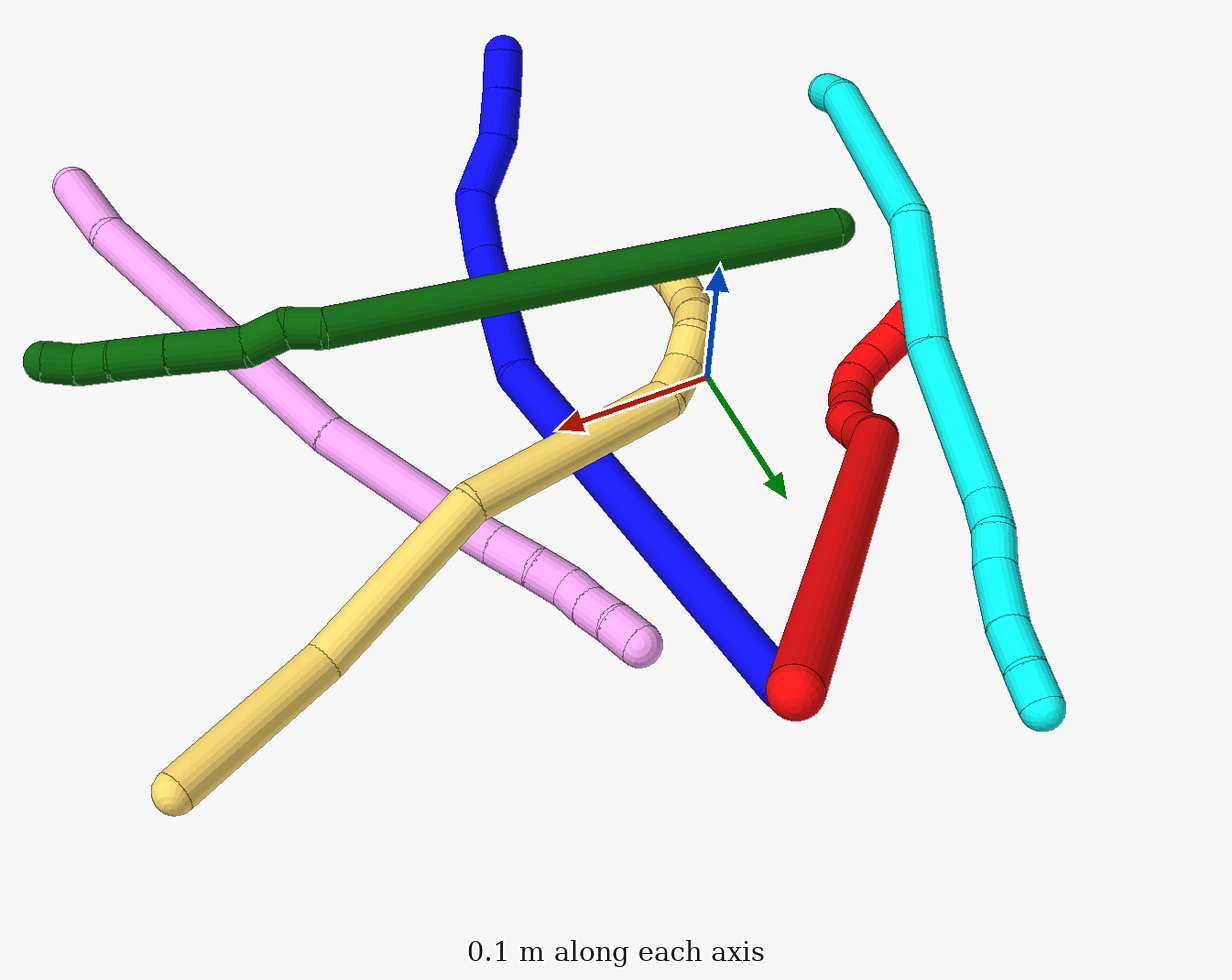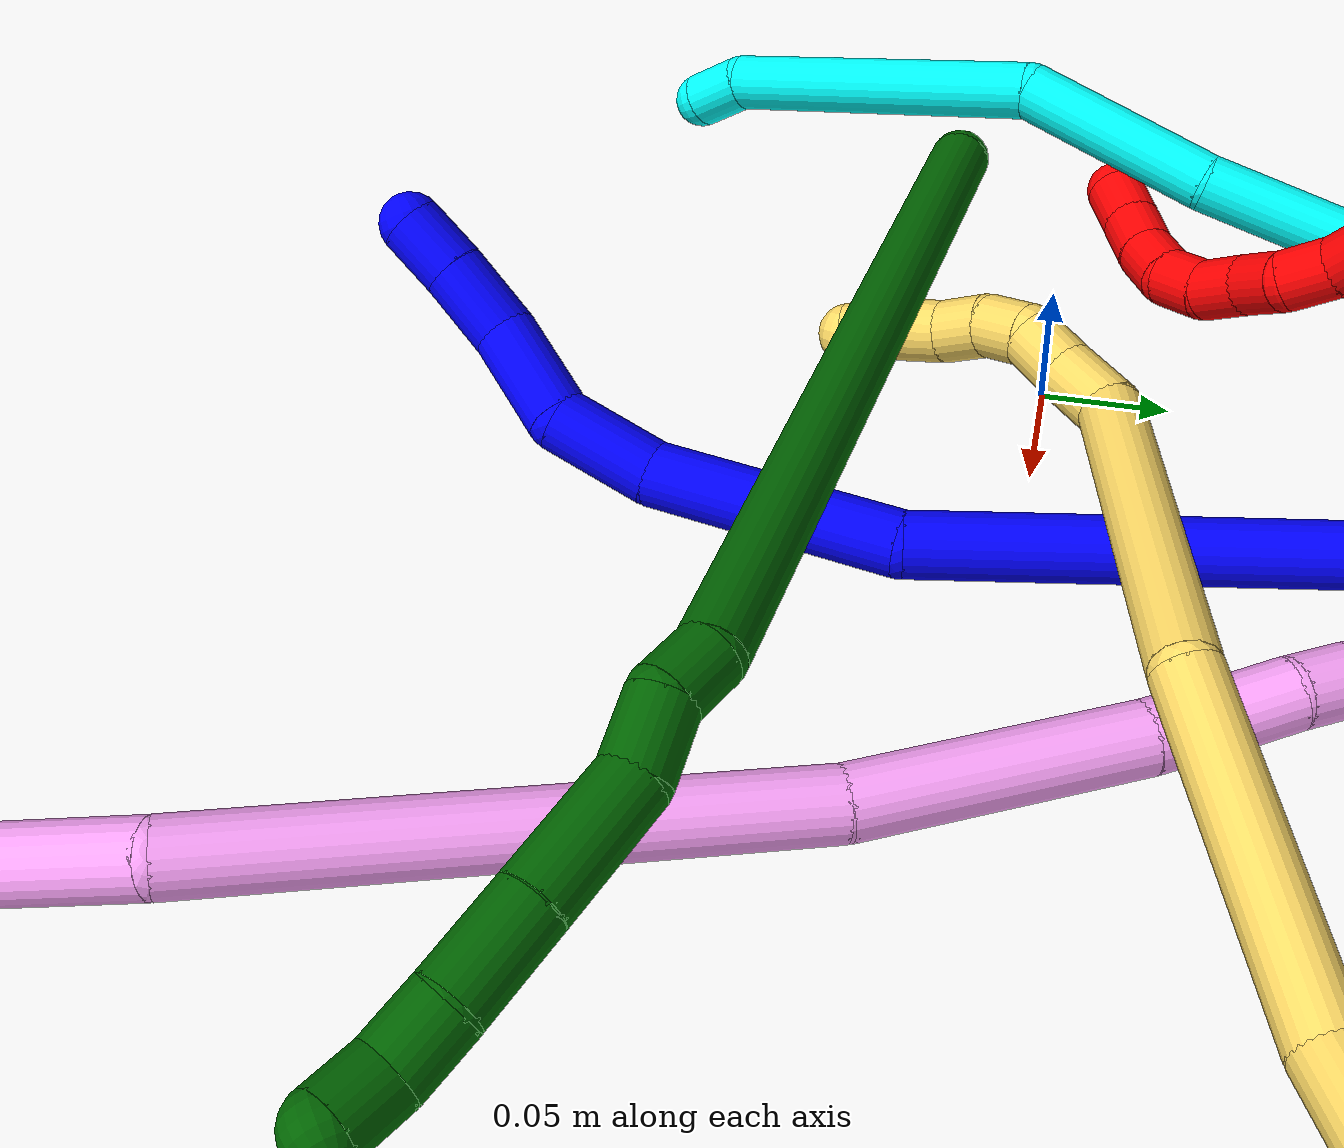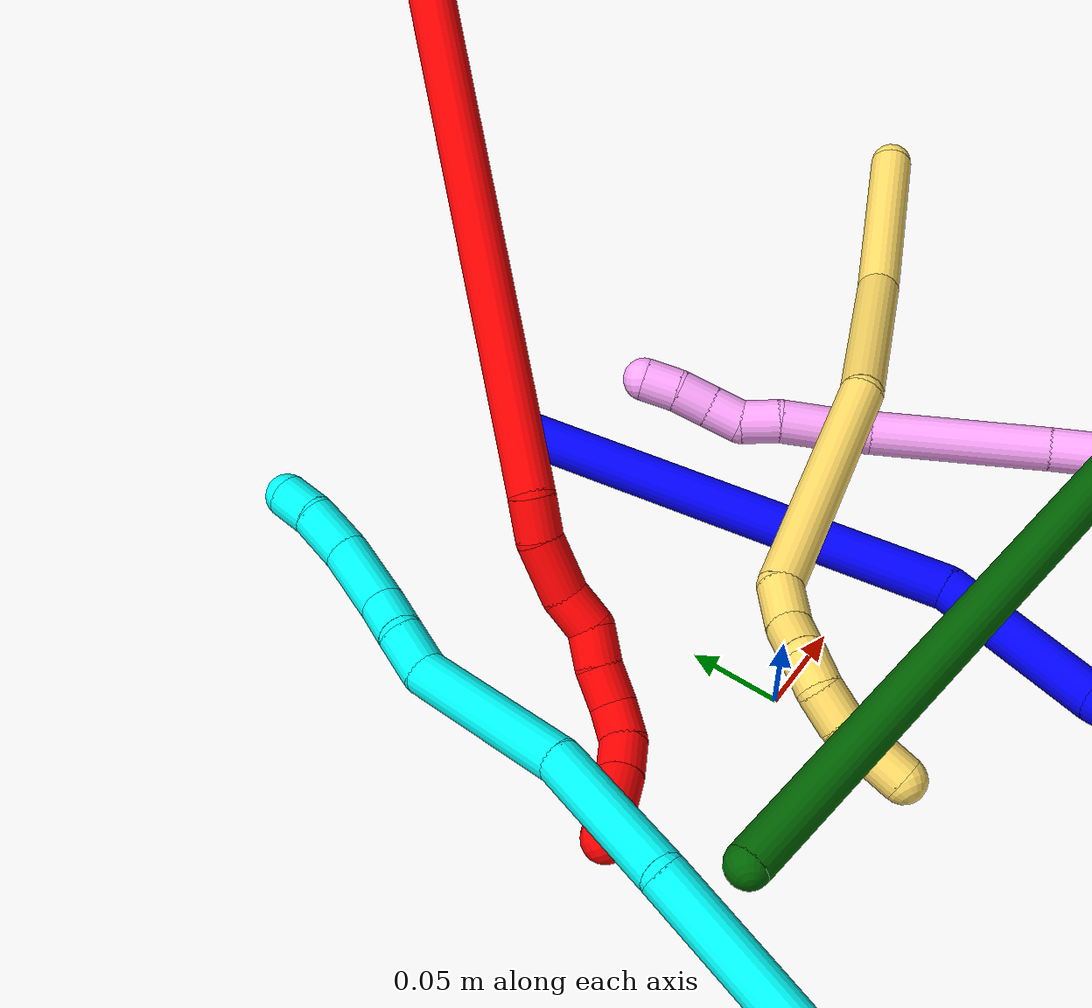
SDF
<sdf version="1.7">
 <world name="default">
  <plugin name="TubeGeneratorPlugin" filename="libtube_generator_plugin.so"/>
  <model name="photoneo_s_sensor">
   <static>1</static>
   <pose>0 0 2 1.57079 1.57079 3.14159</pose>
   <link name="link">
    <inertial><mass>0.1</mass></inertial>
    <sensor name="sensor" type="depth">
     <update_rate>30</update_rate>
     <camera>
      <horizontal_fov>1.22</horizontal_fov>
      <image><width>1920</width><height>1200</height><format>B8G8R8</format></image>
      <clip><near>0.1</near><far>4</far></clip>
      <depth_camera><output>points</output></depth_camera>
     </camera>
     <plugin name="camera_plugin" filename="libgazebo_ros_depth_camera.so">
      <baseline>0.2</baseline>
      <alwaysOn>1</alwaysOn>
      <updateRate>0.0</updateRate>
      <cameraName>camera_ir</cameraName>
      <imageTopicName>/camera/color/image_raw</imageTopicName>
      <cameraInfoTopicName>/camera/color/camera_info</cameraInfoTopicName>
      <depthImageTopicName>/camera/depth/image_raw</depthImageTopicName>
      <depthImageCameraInfoTopicName>/camera/depth/camera_info</depthImageCameraInfoTopicName>
      <pointCloudTopicName>/camera/depth/points</pointCloudTopicName>
      <frameName>fr_optical</frameName>
      <pointCloudCutoff>0.1</pointCloudCutoff>
      <pointCloudCutoffMax>2.0</pointCloudCutoffMax>
      <distortionK1>0</distortionK1>
      <distortionK2>0</distortionK2>
      <distortionK3>0</distortionK3>
      <distortionT1>0</distortionT1>
      <distortionT2>0</distortionT2>
      <CxPrime>0</CxPrime>
      <Cx>0</Cx>
      <Cy>0</Cy>
      <focalLength>0</focalLength>
      <hackBaseline>0</hackBaseline>
     </plugin>
    </sensor>
   </link>
  </model>
  <gravity>0 0 -9.8</gravity>
  <magnetic_field>6e-06 2.3e-05 -4.2e-05</magnetic_field>
  <atmosphere type="adiabatic"/>
  <physics name="default_physics" default="0" type="ode">
   <max_step_size>0.003</max_step_size>
   <real_time_factor>1</real_time_factor>
   <real_time_update_rate>1000</real_time_update_rate>
   <max_contacts>10000</max_contacts>
   <ode>
    <solver>
     <type>quick</type>
     <iters>100</iters>
     <sor>1.3</sor>
     <use_dynamic_moi_rescaling>0</use_dynamic_moi_rescaling>
    </solver>
    <constraints>
     <contact_max_correcting_vel>0</contact_max_correcting_vel>
     <contact_surface_layer>0.001</contact_surface_layer>
     <cfm>0</cfm>
     <erp>0.2</erp>
    </constraints>
   </ode>
  </physics>
  <scene><ambient>0.4 0.4 0.4 1</ambient><background>0.7 0.7 0.7 1</background><shadows>0</shadows></scene>
  <audio><device>default</device></audio>
  <spherical_coordinates>
   <surface_model>EARTH_WGS84</surface_model>
   <latitude_deg>0</latitude_deg>
   <longitude_deg>0</longitude_deg>
   <elevation>0</elevation>
   <heading_deg>0</heading_deg>
  </spherical_coordinates>
  <model name="bin">
   <static>1</static>
   <link name="bottom">
    <collision name="collision-bottom">
     <pose>0 0 -0.01 0 -0 0</pose>
     <geometry><box><size>0.8 0.6 0.02</size></box></geometry>
     <surface>
      <friction><ode><mu>100</mu><mu2>100</mu2></ode></friction>
      <contact><collide_bitmask>65535</collide_bitmask></contact>
     </surface>
    </collision>
   </link>
   <link name="west_wall">
    <collision name="collision-west_wall">
     <pose>-0.41 0 0.1 0 -0 0</pose>
     <geometry><box><size>0.02 0.6 0.2</size></box></geometry>
     <surface>
      <friction><ode><mu>100</mu><mu2>100</mu2></ode></friction>
      <contact><collide_bitmask>65535</collide_bitmask></contact>
     </surface>
    </collision>
   </link>
   <link name="east_wall">
    <collision name="collision-east_wall">
     <pose>0.41 0 0.1 0 -0 0</pose>
     <geometry><box><size>0.02 0.6 0.2</size></box></geometry>
     <surface>
      <friction><ode><mu>100</mu><mu2>100</mu2></ode></friction>
      <contact><collide_bitmask>65535</collide_bitmask></contact>
     </surface>
    </collision>
   </link>
   <link name="south_wall">
    <collision name="collision-south_wall">
     <pose>0 -0.31 0.1 0 -0 0</pose>
     <geometry><box><size>0.8 0.02 0.2</size></box></geometry>
     <surface>
      <friction><ode><mu>100</mu><mu2>100</mu2></ode></friction>
      <contact><collide_bitmask>65535</collide_bitmask></contact>
     </surface>
    </collision>
   </link>
   <link name="north_wall">
    <collision name="collision-north_wall">
     <pose>0 0.31 0.1 0 -0 0</pose>
     <geometry><box><size>0.8 0.02 0.2</size></box></geometry>
     <surface>
      <friction><ode><mu>100</mu><mu2>100</mu2></ode></friction>
      <contact><collide_bitmask>65535</collide_bitmask></contact>
     </surface>
    </collision>
   </link>
  </model>
  <model name="1">
   <static>0</static>
   <link name="1">
    <collision name="collision-cylinder-e_1_1_4">
     <pose>0.028502 -0.117273 0.049514 1.17129 0.220272 0.14643</pose>
     <geometry><cylinder><radius>0.0125</radius><length>0.260898</length></cylinder></geometry>
     <surface>
      <friction><ode><mu>1.16</mu><mu2>1.16</mu2><slip1>0</slip1><slip2>0</slip2></ode></friction>
      <contact><ode><kp>1e+06</kp><kd>1</kd><max_vel>0</max_vel><min_depth>0.001</min_depth></ode></contact>
     </surface>
    </collision>
    <visual name="visual-cylinder-e_1_1_4">
     <pose>0.028502 -0.117273 0.049514 1.17129 0.220272 0.14643</pose>
     <geometry><cylinder><radius>0.0125</radius><length>0.260898</length></cylinder></geometry>
     <material><ambient>0 0 1 1</ambient></material>
    </visual>
    <collision name="collision-cylinder-e_2_4_5">
     <pose>0.052084 -0.27544 0.125671 0.993369 -0.10047 -0.054488</pose>
     <geometry><cylinder><radius>0.0125</radius><length>0.098111</length></cylinder></geometry>
     <surface>
      <friction><ode><mu>1.16</mu><mu2>1.16</mu2><slip1>0</slip1><slip2>0</slip2></ode></friction>
      <contact><ode><kp>1e+06</kp><kd>1</kd><max_vel>0</max_vel><min_depth>0.001</min_depth></ode></contact>
     </surface>
    </collision>
    <visual name="visual-cylinder-e_2_4_5">
     <pose>0.052084 -0.27544 0.125671 0.993369 -0.10047 -0.054488</pose>
     <geometry><cylinder><radius>0.0125</radius><length>0.098111</length></cylinder></geometry>
     <material><ambient>0 0 1 1</ambient></material>
    </visual>
    <collision name="collision-cylinder-e_3_5_6">
     <pose>0.04717 -0.329836 0.16795 0.712247 0.000265 9.9e-05</pose>
     <geometry><cylinder><radius>0.0125</radius><length>0.041316</length></cylinder></geometry>
     <surface>
      <friction><ode><mu>1.16</mu><mu2>1.16</mu2><slip1>0</slip1><slip2>0</slip2></ode></friction>
      <contact><ode><kp>1e+06</kp><kd>1</kd><max_vel>0</max_vel><min_depth>0.001</min_depth></ode></contact>
     </surface>
    </collision>
    <visual name="visual-cylinder-e_3_5_6">
     <pose>0.04717 -0.329836 0.16795 0.712247 0.000265 9.9e-05</pose>
     <geometry><cylinder><radius>0.0125</radius><length>0.041316</length></cylinder></geometry>
     <material><ambient>0 0 1 1</ambient></material>
    </visual>
    <collision name="collision-cylinder-e_4_6_7">
     <pose>0.039185 -0.350615 0.202302 0.370893 -0.378681 -0.071872</pose>
     <geometry><cylinder><radius>0.0125</radius><length>0.043225</length></cylinder></geometry>
     <surface>
      <friction><ode><mu>1.16</mu><mu2>1.16</mu2><slip1>0</slip1><slip2>0</slip2></ode></friction>
      <contact><ode><kp>1e+06</kp><kd>1</kd><max_vel>0</max_vel><min_depth>0.001</min_depth></ode></contact>
     </surface>
    </collision>
    <visual name="visual-cylinder-e_4_6_7">
     <pose>0.039185 -0.350615 0.202302 0.370893 -0.378681 -0.071872</pose>
     <geometry><cylinder><radius>0.0125</radius><length>0.043225</length></cylinder></geometry>
     <material><ambient>0 0 1 1</ambient></material>
    </visual>
    <collision name="collision-cylinder-e_5_7_8">
     <pose>0.030592 -0.363217 0.235863 0.344285 -0.038195 -0.006642</pose>
     <geometry><cylinder><radius>0.0125</radius><length>0.031564</length></cylinder></geometry>
     <surface>
      <friction><ode><mu>1.16</mu><mu2>1.16</mu2><slip1>0</slip1><slip2>0</slip2></ode></friction>
      <contact><ode><kp>1e+06</kp><kd>1</kd><max_vel>0</max_vel><min_depth>0.001</min_depth></ode></contact>
     </surface>
    </collision>
    <visual name="visual-cylinder-e_5_7_8">
     <pose>0.030592 -0.363217 0.235863 0.344285 -0.038195 -0.006642</pose>
     <geometry><cylinder><radius>0.0125</radius><length>0.031564</length></cylinder></geometry>
     <material><ambient>0 0 1 1</ambient></material>
    </visual>
    <collision name="collision-cylinder-e_6_8_2">
     <pose>0.029752 -0.373361 0.262176 0.397974 -0.019114 -0.003855</pose>
     <geometry><cylinder><radius>0.0125</radius><length>0.024885</length></cylinder></geometry>
     <surface>
      <friction><ode><mu>1.16</mu><mu2>1.16</mu2><slip1>0</slip1><slip2>0</slip2></ode></friction>
      <contact><ode><kp>1e+06</kp><kd>1</kd><max_vel>0</max_vel><min_depth>0.001</min_depth></ode></contact>
     </surface>
    </collision>
    <visual name="visual-cylinder-e_6_8_2">
     <pose>0.029752 -0.373361 0.262176 0.397974 -0.019114 -0.003855</pose>
     <geometry><cylinder><radius>0.0125</radius><length>0.024885</length></cylinder></geometry>
     <material><ambient>0 0 1 1</ambient></material>
    </visual>
    <collision name="collision-sphere-2">
     <pose>0.029514 -0.378182 0.273645 0 -0 0</pose>
     <geometry><sphere><radius>0.0125</radius></sphere></geometry>
     <surface>
      <friction><ode><mu>1.16</mu><mu2>1.16</mu2><slip1>0</slip1><slip2>0</slip2></ode></friction>
      <contact><ode><kp>1e+06</kp><kd>1</kd><max_vel>0</max_vel><min_depth>0.001</min_depth></ode></contact>
     </surface>
    </collision>
    <visual name="visual-sphere-2">
     <pose>0.029514 -0.378182 0.273645 0 -0 0</pose>
     <geometry><sphere><radius>0.0125</radius></sphere></geometry>
     <material><ambient>0 0 1 1</ambient></material>
    </visual>
    <collision name="collision-sphere-4">
     <pose>0.057005 -0.234545 0.099028 0 -0 0</pose>
     <geometry><sphere><radius>0.0125</radius></sphere></geometry>
     <surface>
      <friction><ode><mu>1.16</mu><mu2>1.16</mu2><slip1>0</slip1><slip2>0</slip2></ode></friction>
      <contact><ode><kp>1e+06</kp><kd>1</kd><max_vel>0</max_vel><min_depth>0.001</min_depth></ode></contact>
     </surface>
    </collision>
    <visual name="visual-sphere-4">
     <pose>0.057005 -0.234545 0.099028 0 -0 0</pose>
     <geometry><sphere><radius>0.0125</radius></sphere></geometry>
     <material><ambient>0 0 1 1</ambient></material>
    </visual>
    <collision name="collision-sphere-1">
     <geometry><sphere><radius>0.0125</radius></sphere></geometry>
     <surface>
      <friction><ode><mu>1.16</mu><mu2>1.16</mu2><slip1>0</slip1><slip2>0</slip2></ode></friction>
      <contact><ode><kp>1e+06</kp><kd>1</kd><max_vel>0</max_vel><min_depth>0.001</min_depth></ode></contact>
     </surface>
    </collision>
    <visual name="visual-sphere-1">
     <geometry><sphere><radius>0.0125</radius></sphere></geometry>
     <material><ambient>0 0 1 1</ambient></material>
    </visual>
    <collision name="collision-sphere-8">
     <pose>0.02999 -0.36854 0.250708 0 -0 0</pose>
     <geometry><sphere><radius>0.0125</radius></sphere></geometry>
     <surface>
      <friction><ode><mu>1.16</mu><mu2>1.16</mu2><slip1>0</slip1><slip2>0</slip2></ode></friction>
      <contact><ode><kp>1e+06</kp><kd>1</kd><max_vel>0</max_vel><min_depth>0.001</min_depth></ode></contact>
     </surface>
    </collision>
    <visual name="visual-sphere-8">
     <pose>0.02999 -0.36854 0.250708 0 -0 0</pose>
     <geometry><sphere><radius>0.0125</radius></sphere></geometry>
     <material><ambient>0 0 1 1</ambient></material>
    </visual>
    <collision name="collision-sphere-5">
     <pose>0.047164 -0.316335 0.152314 0 -0 0</pose>
     <geometry><sphere><radius>0.0125</radius></sphere></geometry>
     <surface>
      <friction><ode><mu>1.16</mu><mu2>1.16</mu2><slip1>0</slip1><slip2>0</slip2></ode></friction>
      <contact><ode><kp>1e+06</kp><kd>1</kd><max_vel>0</max_vel><min_depth>0.001</min_depth></ode></contact>
     </surface>
    </collision>
    <visual name="visual-sphere-5">
     <pose>0.047164 -0.316335 0.152314 0 -0 0</pose>
     <geometry><sphere><radius>0.0125</radius></sphere></geometry>
     <material><ambient>0 0 1 1</ambient></material>
    </visual>
    <collision name="collision-sphere-6">
     <pose>0.047175 -0.343337 0.183586 0 -0 0</pose>
     <geometry><sphere><radius>0.0125</radius></sphere></geometry>
     <surface>
      <friction><ode><mu>1.16</mu><mu2>1.16</mu2><slip1>0</slip1><slip2>0</slip2></ode></friction>
      <contact><ode><kp>1e+06</kp><kd>1</kd><max_vel>0</max_vel><min_depth>0.001</min_depth></ode></contact>
     </surface>
    </collision>
    <visual name="visual-sphere-6">
     <pose>0.047175 -0.343337 0.183586 0 -0 0</pose>
     <geometry><sphere><radius>0.0125</radius></sphere></geometry>
     <material><ambient>0 0 1 1</ambient></material>
    </visual>
    <collision name="collision-sphere-7">
     <pose>0.031195 -0.357894 0.221018 0 -0 0</pose>
     <geometry><sphere><radius>0.0125</radius></sphere></geometry>
     <surface>
      <friction><ode><mu>1.16</mu><mu2>1.16</mu2><slip1>0</slip1><slip2>0</slip2></ode></friction>
      <contact><ode><kp>1e+06</kp><kd>1</kd><max_vel>0</max_vel><min_depth>0.001</min_depth></ode></contact>
     </surface>
    </collision>
    <visual name="visual-sphere-7">
     <pose>0.031195 -0.357894 0.221018 0 -0 0</pose>
     <geometry><sphere><radius>0.0125</radius></sphere></geometry>
     <material><ambient>0 0 1 1</ambient></material>
    </visual>
    <inertial>
     <pose>0.03579 -0.214318 0.109801 0 -0 0</pose>
     <mass>0.5</mass>
     <inertia>
      <ixx>0.001751</ixx>
      <ixy>0</ixy>
      <ixz>0</ixz>
      <iyy>0.000859</iyy>
      <iyz>0</iyz>
      <izz>0.001126</izz>
     </inertia>
    </inertial>
   </link>
   <pose>0.067109 0.216302 0.011496 0.522264 -0.500517 -0.090772</pose>
  </model>
  <model name="2">
   <static>0</static>
   <link name="2">
    <collision name="collision-cylinder-e_1_1_4">
     <pose>-0.011908 -0.005031 -0.149684 3.10799 -0.079341 -2.34072</pose>
     <geometry><cylinder><radius>0.0125</radius><length>0.300483</length></cylinder></geometry>
     <surface>
      <friction><ode><mu>1.16</mu><mu2>1.16</mu2><slip1>0</slip1><slip2>0</slip2></ode></friction>
      <contact><ode><kp>1e+06</kp><kd>1</kd><max_vel>0</max_vel><min_depth>0.001</min_depth></ode></contact>
     </surface>
    </collision>
    <visual name="visual-cylinder-e_1_1_4">
     <pose>-0.011908 -0.005031 -0.149684 3.10799 -0.079341 -2.34072</pose>
     <geometry><cylinder><radius>0.0125</radius><length>0.300483</length></cylinder></geometry>
     <material><ambient>1 0 0 1</ambient></material>
    </visual>
    <collision name="collision-cylinder-e_2_4_5">
     <pose>-0.027116 -0.007721 -0.31012 -2.92715 -0.291436 1.87599</pose>
     <geometry><cylinder><radius>0.0125</radius><length>0.022976</length></cylinder></geometry>
     <surface>
      <friction><ode><mu>1.16</mu><mu2>1.16</mu2><slip1>0</slip1><slip2>0</slip2></ode></friction>
      <contact><ode><kp>1e+06</kp><kd>1</kd><max_vel>0</max_vel><min_depth>0.001</min_depth></ode></contact>
     </surface>
    </collision>
    <visual name="visual-cylinder-e_2_4_5">
     <pose>-0.027116 -0.007721 -0.31012 -2.92715 -0.291436 1.87599</pose>
     <geometry><cylinder><radius>0.0125</radius><length>0.022976</length></cylinder></geometry>
     <material><ambient>1 0 0 1</ambient></material>
    </visual>
    <collision name="collision-cylinder-e_3_5_6">
     <pose>-0.032703 0.001153 -0.335614 -2.72451 -0.140797 0.6433</pose>
     <geometry><cylinder><radius>0.0125</radius><length>0.032572</length></cylinder></geometry>
     <surface>
      <friction><ode><mu>1.16</mu><mu2>1.16</mu2><slip1>0</slip1><slip2>0</slip2></ode></friction>
      <contact><ode><kp>1e+06</kp><kd>1</kd><max_vel>0</max_vel><min_depth>0.001</min_depth></ode></contact>
     </surface>
    </collision>
    <visual name="visual-cylinder-e_3_5_6">
     <pose>-0.032703 0.001153 -0.335614 -2.72451 -0.140797 0.6433</pose>
     <geometry><cylinder><radius>0.0125</radius><length>0.032572</length></cylinder></geometry>
     <material><ambient>1 0 0 1</ambient></material>
    </visual>
    <collision name="collision-cylinder-e_4_6_7">
     <pose>-0.032986 0.011856 -0.360003 -2.73345 0.188266 -0.856005</pose>
     <geometry><cylinder><radius>0.0125</radius><length>0.021396</length></cylinder></geometry>
     <surface>
      <friction><ode><mu>1.16</mu><mu2>1.16</mu2><slip1>0</slip1><slip2>0</slip2></ode></friction>
      <contact><ode><kp>1e+06</kp><kd>1</kd><max_vel>0</max_vel><min_depth>0.001</min_depth></ode></contact>
     </surface>
    </collision>
    <visual name="visual-cylinder-e_4_6_7">
     <pose>-0.032986 0.011856 -0.360003 -2.73345 0.188266 -0.856005</pose>
     <geometry><cylinder><radius>0.0125</radius><length>0.021396</length></cylinder></geometry>
     <material><ambient>1 0 0 1</ambient></material>
    </visual>
    <collision name="collision-cylinder-e_5_7_8">
     <pose>-0.0322 0.016109 -0.379752 -3.13346 -0.119807 3.00626</pose>
     <geometry><cylinder><radius>0.0125</radius><length>0.020354</length></cylinder></geometry>
     <surface>
      <friction><ode><mu>1.16</mu><mu2>1.16</mu2><slip1>0</slip1><slip2>0</slip2></ode></friction>
      <contact><ode><kp>1e+06</kp><kd>1</kd><max_vel>0</max_vel><min_depth>0.001</min_depth></ode></contact>
     </surface>
    </collision>
    <visual name="visual-cylinder-e_5_7_8">
     <pose>-0.0322 0.016109 -0.379752 -3.13346 -0.119807 3.00626</pose>
     <geometry><cylinder><radius>0.0125</radius><length>0.020354</length></cylinder></geometry>
     <material><ambient>1 0 0 1</ambient></material>
    </visual>
    <collision name="collision-cylinder-e_6_8_9">
     <pose>-0.033394 0.017473 -0.400506 -3.02182 0.002101 -0.035037</pose>
     <geometry><cylinder><radius>0.0125</radius><length>0.021454</length></cylinder></geometry>
     <surface>
      <friction><ode><mu>1.16</mu><mu2>1.16</mu2><slip1>0</slip1><slip2>0</slip2></ode></friction>
      <contact><ode><kp>1e+06</kp><kd>1</kd><max_vel>0</max_vel><min_depth>0.001</min_depth></ode></contact>
     </surface>
    </collision>
    <visual name="visual-cylinder-e_6_8_9">
     <pose>-0.033394 0.017473 -0.400506 -3.02182 0.002101 -0.035037</pose>
     <geometry><cylinder><radius>0.0125</radius><length>0.021454</length></cylinder></geometry>
     <material><ambient>1 0 0 1</ambient></material>
    </visual>
    <collision name="collision-cylinder-e_7_9_10">
     <pose>-0.03161 0.016421 -0.420738 2.90268 0.176786 1.27204</pose>
     <geometry><cylinder><radius>0.0125</radius><length>0.020036</length></cylinder></geometry>
     <surface>
      <friction><ode><mu>1.16</mu><mu2>1.16</mu2><slip1>0</slip1><slip2>0</slip2></ode></friction>
      <contact><ode><kp>1e+06</kp><kd>1</kd><max_vel>0</max_vel><min_depth>0.001</min_depth></ode></contact>
     </surface>
    </collision>
    <visual name="visual-cylinder-e_7_9_10">
     <pose>-0.03161 0.016421 -0.420738 2.90268 0.176786 1.27204</pose>
     <geometry><cylinder><radius>0.0125</radius><length>0.020036</length></cylinder></geometry>
     <material><ambient>1 0 0 1</ambient></material>
    </visual>
    <collision name="collision-cylinder-e_8_10_11">
     <pose>-0.029631 0.008314 -0.438485 2.52622 0.021646 0.068091</pose>
     <geometry><cylinder><radius>0.0125</radius><length>0.020006</length></cylinder></geometry>
     <surface>
      <friction><ode><mu>1.16</mu><mu2>1.16</mu2><slip1>0</slip1><slip2>0</slip2></ode></friction>
      <contact><ode><kp>1e+06</kp><kd>1</kd><max_vel>0</max_vel><min_depth>0.001</min_depth></ode></contact>
     </surface>
    </collision>
    <visual name="visual-cylinder-e_8_10_11">
     <pose>-0.029631 0.008314 -0.438485 2.52622 0.021646 0.068091</pose>
     <geometry><cylinder><radius>0.0125</radius><length>0.020006</length></cylinder></geometry>
     <material><ambient>1 0 0 1</ambient></material>
    </visual>
    <collision name="collision-cylinder-e_9_11_12">
     <pose>-0.02911 -0.004717 -0.453766 2.34625 0.030015 0.07143</pose>
     <geometry><cylinder><radius>0.0125</radius><length>0.020336</length></cylinder></geometry>
     <surface>
      <friction><ode><mu>1.16</mu><mu2>1.16</mu2><slip1>0</slip1><slip2>0</slip2></ode></friction>
      <contact><ode><kp>1e+06</kp><kd>1</kd><max_vel>0</max_vel><min_depth>0.001</min_depth></ode></contact>
     </surface>
    </collision>
    <visual name="visual-cylinder-e_9_11_12">
     <pose>-0.02911 -0.004717 -0.453766 2.34625 0.030015 0.07143</pose>
     <geometry><cylinder><radius>0.0125</radius><length>0.020336</length></cylinder></geometry>
     <material><ambient>1 0 0 1</ambient></material>
    </visual>
    <collision name="collision-cylinder-e_10_12_2">
     <pose>-0.027441 -0.019417 -0.467712 2.31342 0.134193 0.30344</pose>
     <geometry><cylinder><radius>0.0125</radius><length>0.020387</length></cylinder></geometry>
     <surface>
      <friction><ode><mu>1.16</mu><mu2>1.16</mu2><slip1>0</slip1><slip2>0</slip2></ode></friction>
      <contact><ode><kp>1e+06</kp><kd>1</kd><max_vel>0</max_vel><min_depth>0.001</min_depth></ode></contact>
     </surface>
    </collision>
    <visual name="visual-cylinder-e_10_12_2">
     <pose>-0.027441 -0.019417 -0.467712 2.31342 0.134193 0.30344</pose>
     <geometry><cylinder><radius>0.0125</radius><length>0.020387</length></cylinder></geometry>
     <material><ambient>1 0 0 1</ambient></material>
    </visual>
    <collision name="collision-sphere-2">
     <pose>-0.026077 -0.026859 -0.474543 0 -0 0</pose>
     <geometry><sphere><radius>0.0125</radius></sphere></geometry>
     <surface>
      <friction><ode><mu>1.16</mu><mu2>1.16</mu2><slip1>0</slip1><slip2>0</slip2></ode></friction>
      <contact><ode><kp>1e+06</kp><kd>1</kd><max_vel>0</max_vel><min_depth>0.001</min_depth></ode></contact>
     </surface>
    </collision>
    <visual name="visual-sphere-2">
     <pose>-0.026077 -0.026859 -0.474543 0 -0 0</pose>
     <geometry><sphere><radius>0.0125</radius></sphere></geometry>
     <material><ambient>1 0 0 1</ambient></material>
    </visual>
    <collision name="collision-sphere-12">
     <pose>-0.028805 -0.011975 -0.460881 0 -0 0</pose>
     <geometry><sphere><radius>0.0125</radius></sphere></geometry>
     <surface>
      <friction><ode><mu>1.16</mu><mu2>1.16</mu2><slip1>0</slip1><slip2>0</slip2></ode></friction>
      <contact><ode><kp>1e+06</kp><kd>1</kd><max_vel>0</max_vel><min_depth>0.001</min_depth></ode></contact>
     </surface>
    </collision>
    <visual name="visual-sphere-12">
     <pose>-0.028805 -0.011975 -0.460881 0 -0 0</pose>
     <geometry><sphere><radius>0.0125</radius></sphere></geometry>
     <material><ambient>1 0 0 1</ambient></material>
    </visual>
    <collision name="collision-sphere-11">
     <pose>-0.029415 0.002541 -0.446651 0 -0 0</pose>
     <geometry><sphere><radius>0.0125</radius></sphere></geometry>
     <surface>
      <friction><ode><mu>1.16</mu><mu2>1.16</mu2><slip1>0</slip1><slip2>0</slip2></ode></friction>
      <contact><ode><kp>1e+06</kp><kd>1</kd><max_vel>0</max_vel><min_depth>0.001</min_depth></ode></contact>
     </surface>
    </collision>
    <visual name="visual-sphere-11">
     <pose>-0.029415 0.002541 -0.446651 0 -0 0</pose>
     <geometry><sphere><radius>0.0125</radius></sphere></geometry>
     <material><ambient>1 0 0 1</ambient></material>
    </visual>
    <collision name="collision-sphere-10">
     <pose>-0.029848 0.014087 -0.430319 0 -0 0</pose>
     <geometry><sphere><radius>0.0125</radius></sphere></geometry>
     <surface>
      <friction><ode><mu>1.16</mu><mu2>1.16</mu2><slip1>0</slip1><slip2>0</slip2></ode></friction>
      <contact><ode><kp>1e+06</kp><kd>1</kd><max_vel>0</max_vel><min_depth>0.001</min_depth></ode></contact>
     </surface>
    </collision>
    <visual name="visual-sphere-10">
     <pose>-0.029848 0.014087 -0.430319 0 -0 0</pose>
     <geometry><sphere><radius>0.0125</radius></sphere></geometry>
     <material><ambient>1 0 0 1</ambient></material>
    </visual>
    <collision name="collision-sphere-9">
     <pose>-0.033372 0.018755 -0.411156 0 -0 0</pose>
     <geometry><sphere><radius>0.0125</radius></sphere></geometry>
     <surface>
      <friction><ode><mu>1.16</mu><mu2>1.16</mu2><slip1>0</slip1><slip2>0</slip2></ode></friction>
      <contact><ode><kp>1e+06</kp><kd>1</kd><max_vel>0</max_vel><min_depth>0.001</min_depth></ode></contact>
     </surface>
    </collision>
    <visual name="visual-sphere-9">
     <pose>-0.033372 0.018755 -0.411156 0 -0 0</pose>
     <geometry><sphere><radius>0.0125</radius></sphere></geometry>
     <material><ambient>1 0 0 1</ambient></material>
    </visual>
    <collision name="collision-sphere-4">
     <pose>-0.023816 -0.010063 -0.299368 0 -0 0</pose>
     <geometry><sphere><radius>0.0125</radius></sphere></geometry>
     <surface>
      <friction><ode><mu>1.16</mu><mu2>1.16</mu2><slip1>0</slip1><slip2>0</slip2></ode></friction>
      <contact><ode><kp>1e+06</kp><kd>1</kd><max_vel>0</max_vel><min_depth>0.001</min_depth></ode></contact>
     </surface>
    </collision>
    <visual name="visual-sphere-4">
     <pose>-0.023816 -0.010063 -0.299368 0 -0 0</pose>
     <geometry><sphere><radius>0.0125</radius></sphere></geometry>
     <material><ambient>1 0 0 1</ambient></material>
    </visual>
    <collision name="collision-sphere-1">
     <geometry><sphere><radius>0.0125</radius></sphere></geometry>
     <surface>
      <friction><ode><mu>1.16</mu><mu2>1.16</mu2><slip1>0</slip1><slip2>0</slip2></ode></friction>
      <contact><ode><kp>1e+06</kp><kd>1</kd><max_vel>0</max_vel><min_depth>0.001</min_depth></ode></contact>
     </surface>
    </collision>
    <visual name="visual-sphere-1">
     <geometry><sphere><radius>0.0125</radius></sphere></geometry>
     <material><ambient>1 0 0 1</ambient></material>
    </visual>
    <collision name="collision-sphere-8">
     <pose>-0.033417 0.016191 -0.389855 0 -0 0</pose>
     <geometry><sphere><radius>0.0125</radius></sphere></geometry>
     <surface>
      <friction><ode><mu>1.16</mu><mu2>1.16</mu2><slip1>0</slip1><slip2>0</slip2></ode></friction>
      <contact><ode><kp>1e+06</kp><kd>1</kd><max_vel>0</max_vel><min_depth>0.001</min_depth></ode></contact>
     </surface>
    </collision>
    <visual name="visual-sphere-8">
     <pose>-0.033417 0.016191 -0.389855 0 -0 0</pose>
     <geometry><sphere><radius>0.0125</radius></sphere></geometry>
     <material><ambient>1 0 0 1</ambient></material>
    </visual>
    <collision name="collision-sphere-5">
     <pose>-0.030417 -0.005379 -0.320872 0 -0 0</pose>
     <geometry><sphere><radius>0.0125</radius></sphere></geometry>
     <surface>
      <friction><ode><mu>1.16</mu><mu2>1.16</mu2><slip1>0</slip1><slip2>0</slip2></ode></friction>
      <contact><ode><kp>1e+06</kp><kd>1</kd><max_vel>0</max_vel><min_depth>0.001</min_depth></ode></contact>
     </surface>
    </collision>
    <visual name="visual-sphere-5">
     <pose>-0.030417 -0.005379 -0.320872 0 -0 0</pose>
     <geometry><sphere><radius>0.0125</radius></sphere></geometry>
     <material><ambient>1 0 0 1</ambient></material>
    </visual>
    <collision name="collision-sphere-6">
     <pose>-0.034988 0.007685 -0.350357 0 -0 0</pose>
     <geometry><sphere><radius>0.0125</radius></sphere></geometry>
     <surface>
      <friction><ode><mu>1.16</mu><mu2>1.16</mu2><slip1>0</slip1><slip2>0</slip2></ode></friction>
      <contact><ode><kp>1e+06</kp><kd>1</kd><max_vel>0</max_vel><min_depth>0.001</min_depth></ode></contact>
     </surface>
    </collision>
    <visual name="visual-sphere-6">
     <pose>-0.034988 0.007685 -0.350357 0 -0 0</pose>
     <geometry><sphere><radius>0.0125</radius></sphere></geometry>
     <material><ambient>1 0 0 1</ambient></material>
    </visual>
    <collision name="collision-sphere-7">
     <pose>-0.030984 0.016027 -0.369648 0 -0 0</pose>
     <geometry><sphere><radius>0.0125</radius></sphere></geometry>
     <surface>
      <friction><ode><mu>1.16</mu><mu2>1.16</mu2><slip1>0</slip1><slip2>0</slip2></ode></friction>
      <contact><ode><kp>1e+06</kp><kd>1</kd><max_vel>0</max_vel><min_depth>0.001</min_depth></ode></contact>
     </surface>
    </collision>
    <visual name="visual-sphere-7">
     <pose>-0.030984 0.016027 -0.369648 0 -0 0</pose>
     <geometry><sphere><radius>0.0125</radius></sphere></geometry>
     <material><ambient>1 0 0 1</ambient></material>
    </visual>
    <inertial>
     <pose>-0.019443 -0.001383 -0.246049 0 -0 0</pose>
     <mass>0.5</mass>
     <inertia>
      <ixx>-0.003192</ixx>
      <ixy>0</ixy>
      <ixz>0</ixz>
      <iyy>-4.5e-05</iyy>
      <iyz>0</iyz>
      <izz>0.00022</izz>
     </inertia>
    </inertial>
   </link>
   <pose>0.149463 0.334585 0.242595 -0.890028 -0.7324 -1.13101</pose>
  </model>
  <model name="3">
   <static>0</static>
   <link name="3">
    <collision name="collision-cylinder-e_1_1_4">
     <pose>-0.000288 -7e-06 0.012324 0.000545 -0.02337 -6e-06</pose>
     <geometry><cylinder><radius>0.0125</radius><length>0.024654</length></cylinder></geometry>
     <surface>
      <friction><ode><mu>1.16</mu><mu2>1.16</mu2><slip1>0</slip1><slip2>0</slip2></ode></friction>
      <contact><ode><kp>1e+06</kp><kd>1</kd><max_vel>0</max_vel><min_depth>0.001</min_depth></ode></contact>
     </surface>
    </collision>
    <visual name="visual-cylinder-e_1_1_4">
     <pose>-0.000288 -7e-06 0.012324 0.000545 -0.02337 -6e-06</pose>
     <geometry><cylinder><radius>0.0125</radius><length>0.024654</length></cylinder></geometry>
     <material><ambient>0.003922 1 0.996078 1</ambient></material>
    </visual>
    <collision name="collision-cylinder-e_2_4_5">
     <pose>0.011048 0.023267 0.091746 -0.333964 0.162235 -0.027403</pose>
     <geometry><cylinder><radius>0.0125</radius><length>0.143935</length></cylinder></geometry>
     <surface>
      <friction><ode><mu>1.16</mu><mu2>1.16</mu2><slip1>0</slip1><slip2>0</slip2></ode></friction>
      <contact><ode><kp>1e+06</kp><kd>1</kd><max_vel>0</max_vel><min_depth>0.001</min_depth></ode></contact>
     </surface>
    </collision>
    <visual name="visual-cylinder-e_2_4_5">
     <pose>0.011048 0.023267 0.091746 -0.333964 0.162235 -0.027403</pose>
     <geometry><cylinder><radius>0.0125</radius><length>0.143935</length></cylinder></geometry>
     <material><ambient>0.003922 1 0.996078 1</ambient></material>
    </visual>
    <collision name="collision-cylinder-e_3_5_6">
     <pose>0.038435 0.073854 0.189357 -0.730014 0.367446 -0.141776</pose>
     <geometry><cylinder><radius>0.0125</radius><length>0.087751</length></cylinder></geometry>
     <surface>
      <friction><ode><mu>1.16</mu><mu2>1.16</mu2><slip1>0</slip1><slip2>0</slip2></ode></friction>
      <contact><ode><kp>1e+06</kp><kd>1</kd><max_vel>0</max_vel><min_depth>0.001</min_depth></ode></contact>
     </surface>
    </collision>
    <visual name="visual-cylinder-e_3_5_6">
     <pose>0.038435 0.073854 0.189357 -0.730014 0.367446 -0.141776</pose>
     <geometry><cylinder><radius>0.0125</radius><length>0.087751</length></cylinder></geometry>
     <material><ambient>0.003922 1 0.996078 1</ambient></material>
    </visual>
    <collision name="collision-cylinder-e_4_6_7">
     <pose>0.062235 0.136342 0.255217 -0.783032 0.15981 -0.066091</pose>
     <geometry><cylinder><radius>0.0125</radius><length>0.10103</length></cylinder></geometry>
     <surface>
      <friction><ode><mu>1.16</mu><mu2>1.16</mu2><slip1>0</slip1><slip2>0</slip2></ode></friction>
      <contact><ode><kp>1e+06</kp><kd>1</kd><max_vel>0</max_vel><min_depth>0.001</min_depth></ode></contact>
     </surface>
    </collision>
    <visual name="visual-cylinder-e_4_6_7">
     <pose>0.062235 0.136342 0.255217 -0.783032 0.15981 -0.066091</pose>
     <geometry><cylinder><radius>0.0125</radius><length>0.10103</length></cylinder></geometry>
     <material><ambient>0.003922 1 0.996078 1</ambient></material>
    </visual>
    <collision name="collision-cylinder-e_5_7_8">
     <pose>0.07436 0.175498 0.302337 -0.325653 0.317785 -0.052638</pose>
     <geometry><cylinder><radius>0.0125</radius><length>0.026161</length></cylinder></geometry>
     <surface>
      <friction><ode><mu>1.16</mu><mu2>1.16</mu2><slip1>0</slip1><slip2>0</slip2></ode></friction>
      <contact><ode><kp>1e+06</kp><kd>1</kd><max_vel>0</max_vel><min_depth>0.001</min_depth></ode></contact>
     </surface>
    </collision>
    <visual name="visual-cylinder-e_5_7_8">
     <pose>0.07436 0.175498 0.302337 -0.325653 0.317785 -0.052638</pose>
     <geometry><cylinder><radius>0.0125</radius><length>0.026161</length></cylinder></geometry>
     <material><ambient>0.003922 1 0.996078 1</ambient></material>
    </visual>
    <collision name="collision-cylinder-e_6_8_9">
     <pose>0.083747 0.185766 0.322446 -0.646593 0.469525 -0.159929</pose>
     <geometry><cylinder><radius>0.0125</radius><length>0.023425</length></cylinder></geometry>
     <surface>
      <friction><ode><mu>1.16</mu><mu2>1.16</mu2><slip1>0</slip1><slip2>0</slip2></ode></friction>
      <contact><ode><kp>1e+06</kp><kd>1</kd><max_vel>0</max_vel><min_depth>0.001</min_depth></ode></contact>
     </surface>
    </collision>
    <visual name="visual-cylinder-e_6_8_9">
     <pose>0.083747 0.185766 0.322446 -0.646593 0.469525 -0.159929</pose>
     <geometry><cylinder><radius>0.0125</radius><length>0.023425</length></cylinder></geometry>
     <material><ambient>0.003922 1 0.996078 1</ambient></material>
    </visual>
    <collision name="collision-cylinder-e_7_9_10">
     <pose>0.095947 0.200497 0.348006 -0.4556 0.345371 -0.080827</pose>
     <geometry><cylinder><radius>0.0125</radius><length>0.040766</length></cylinder></geometry>
     <surface>
      <friction><ode><mu>1.16</mu><mu2>1.16</mu2><slip1>0</slip1><slip2>0</slip2></ode></friction>
      <contact><ode><kp>1e+06</kp><kd>1</kd><max_vel>0</max_vel><min_depth>0.001</min_depth></ode></contact>
     </surface>
    </collision>
    <visual name="visual-cylinder-e_7_9_10">
     <pose>0.095947 0.200497 0.348006 -0.4556 0.345371 -0.080827</pose>
     <geometry><cylinder><radius>0.0125</radius><length>0.040766</length></cylinder></geometry>
     <material><ambient>0.003922 1 0.996078 1</ambient></material>
    </visual>
    <collision name="collision-cylinder-e_8_10_11">
     <pose>0.105803 0.214815 0.37853 -0.416133 0.200512 -0.042469</pose>
     <geometry><cylinder><radius>0.0125</radius><length>0.02968</length></cylinder></geometry>
     <surface>
      <friction><ode><mu>1.16</mu><mu2>1.16</mu2><slip1>0</slip1><slip2>0</slip2></ode></friction>
      <contact><ode><kp>1e+06</kp><kd>1</kd><max_vel>0</max_vel><min_depth>0.001</min_depth></ode></contact>
     </surface>
    </collision>
    <visual name="visual-cylinder-e_8_10_11">
     <pose>0.105803 0.214815 0.37853 -0.416133 0.200512 -0.042469</pose>
     <geometry><cylinder><radius>0.0125</radius><length>0.02968</length></cylinder></geometry>
     <material><ambient>0.003922 1 0.996078 1</ambient></material>
    </visual>
    <collision name="collision-cylinder-e_9_11_2">
     <pose>0.110356 0.227239 0.400902 -0.625115 0.141842 -0.045905</pose>
     <geometry><cylinder><radius>0.0125</radius><length>0.022597</length></cylinder></geometry>
     <surface>
      <friction><ode><mu>1.16</mu><mu2>1.16</mu2><slip1>0</slip1><slip2>0</slip2></ode></friction>
      <contact><ode><kp>1e+06</kp><kd>1</kd><max_vel>0</max_vel><min_depth>0.001</min_depth></ode></contact>
     </surface>
    </collision>
    <visual name="visual-cylinder-e_9_11_2">
     <pose>0.110356 0.227239 0.400902 -0.625115 0.141842 -0.045905</pose>
     <geometry><cylinder><radius>0.0125</radius><length>0.022597</length></cylinder></geometry>
     <material><ambient>0.003922 1 0.996078 1</ambient></material>
    </visual>
    <collision name="collision-sphere-2">
     <pose>0.111953 0.233784 0.409972 0 -0 0</pose>
     <geometry><sphere><radius>0.0125</radius></sphere></geometry>
     <surface>
      <friction><ode><mu>1.16</mu><mu2>1.16</mu2><slip1>0</slip1><slip2>0</slip2></ode></friction>
      <contact><ode><kp>1e+06</kp><kd>1</kd><max_vel>0</max_vel><min_depth>0.001</min_depth></ode></contact>
     </surface>
    </collision>
    <visual name="visual-sphere-2">
     <pose>0.111953 0.233784 0.409972 0 -0 0</pose>
     <geometry><sphere><radius>0.0125</radius></sphere></geometry>
     <material><ambient>0.003922 1 0.996078 1</ambient></material>
    </visual>
    <collision name="collision-sphere-11">
     <pose>0.108759 0.220693 0.391832 0 -0 0</pose>
     <geometry><sphere><radius>0.0125</radius></sphere></geometry>
     <surface>
      <friction><ode><mu>1.16</mu><mu2>1.16</mu2><slip1>0</slip1><slip2>0</slip2></ode></friction>
      <contact><ode><kp>1e+06</kp><kd>1</kd><max_vel>0</max_vel><min_depth>0.001</min_depth></ode></contact>
     </surface>
    </collision>
    <visual name="visual-sphere-11">
     <pose>0.108759 0.220693 0.391832 0 -0 0</pose>
     <geometry><sphere><radius>0.0125</radius></sphere></geometry>
     <material><ambient>0.003922 1 0.996078 1</ambient></material>
    </visual>
    <collision name="collision-sphere-10">
     <pose>0.102848 0.208936 0.365229 0 -0 0</pose>
     <geometry><sphere><radius>0.0125</radius></sphere></geometry>
     <surface>
      <friction><ode><mu>1.16</mu><mu2>1.16</mu2><slip1>0</slip1><slip2>0</slip2></ode></friction>
      <contact><ode><kp>1e+06</kp><kd>1</kd><max_vel>0</max_vel><min_depth>0.001</min_depth></ode></contact>
     </surface>
    </collision>
    <visual name="visual-sphere-10">
     <pose>0.102848 0.208936 0.365229 0 -0 0</pose>
     <geometry><sphere><radius>0.0125</radius></sphere></geometry>
     <material><ambient>0.003922 1 0.996078 1</ambient></material>
    </visual>
    <collision name="collision-sphere-9">
     <pose>0.089046 0.192058 0.330783 0 -0 0</pose>
     <geometry><sphere><radius>0.0125</radius></sphere></geometry>
     <surface>
      <friction><ode><mu>1.16</mu><mu2>1.16</mu2><slip1>0</slip1><slip2>0</slip2></ode></friction>
      <contact><ode><kp>1e+06</kp><kd>1</kd><max_vel>0</max_vel><min_depth>0.001</min_depth></ode></contact>
     </surface>
    </collision>
    <visual name="visual-sphere-9">
     <pose>0.089046 0.192058 0.330783 0 -0 0</pose>
     <geometry><sphere><radius>0.0125</radius></sphere></geometry>
     <material><ambient>0.003922 1 0.996078 1</ambient></material>
    </visual>
    <collision name="collision-sphere-4">
     <pose>-0.000576 -1.3e-05 0.024648 0 -0 0</pose>
     <geometry><sphere><radius>0.0125</radius></sphere></geometry>
     <surface>
      <friction><ode><mu>1.16</mu><mu2>1.16</mu2><slip1>0</slip1><slip2>0</slip2></ode></friction>
      <contact><ode><kp>1e+06</kp><kd>1</kd><max_vel>0</max_vel><min_depth>0.001</min_depth></ode></contact>
     </surface>
    </collision>
    <visual name="visual-sphere-4">
     <pose>-0.000576 -1.3e-05 0.024648 0 -0 0</pose>
     <geometry><sphere><radius>0.0125</radius></sphere></geometry>
     <material><ambient>0.003922 1 0.996078 1</ambient></material>
    </visual>
    <collision name="collision-sphere-1">
     <geometry><sphere><radius>0.0125</radius></sphere></geometry>
     <surface>
      <friction><ode><mu>1.16</mu><mu2>1.16</mu2><slip1>0</slip1><slip2>0</slip2></ode></friction>
      <contact><ode><kp>1e+06</kp><kd>1</kd><max_vel>0</max_vel><min_depth>0.001</min_depth></ode></contact>
     </surface>
    </collision>
    <visual name="visual-sphere-1">
     <geometry><sphere><radius>0.0125</radius></sphere></geometry>
     <material><ambient>0.003922 1 0.996078 1</ambient></material>
    </visual>
    <collision name="collision-sphere-8">
     <pose>0.078448 0.179473 0.31411 0 -0 0</pose>
     <geometry><sphere><radius>0.0125</radius></sphere></geometry>
     <surface>
      <friction><ode><mu>1.16</mu><mu2>1.16</mu2><slip1>0</slip1><slip2>0</slip2></ode></friction>
      <contact><ode><kp>1e+06</kp><kd>1</kd><max_vel>0</max_vel><min_depth>0.001</min_depth></ode></contact>
     </surface>
    </collision>
    <visual name="visual-sphere-8">
     <pose>0.078448 0.179473 0.31411 0 -0 0</pose>
     <geometry><sphere><radius>0.0125</radius></sphere></geometry>
     <material><ambient>0.003922 1 0.996078 1</ambient></material>
    </visual>
    <collision name="collision-sphere-5">
     <pose>0.022673 0.046548 0.158845 0 -0 0</pose>
     <geometry><sphere><radius>0.0125</radius></sphere></geometry>
     <surface>
      <friction><ode><mu>1.16</mu><mu2>1.16</mu2><slip1>0</slip1><slip2>0</slip2></ode></friction>
      <contact><ode><kp>1e+06</kp><kd>1</kd><max_vel>0</max_vel><min_depth>0.001</min_depth></ode></contact>
     </surface>
    </collision>
    <visual name="visual-sphere-5">
     <pose>0.022673 0.046548 0.158845 0 -0 0</pose>
     <geometry><sphere><radius>0.0125</radius></sphere></geometry>
     <material><ambient>0.003922 1 0.996078 1</ambient></material>
    </visual>
    <collision name="collision-sphere-6">
     <pose>0.054196 0.101161 0.219869 0 -0 0</pose>
     <geometry><sphere><radius>0.0125</radius></sphere></geometry>
     <surface>
      <friction><ode><mu>1.16</mu><mu2>1.16</mu2><slip1>0</slip1><slip2>0</slip2></ode></friction>
      <contact><ode><kp>1e+06</kp><kd>1</kd><max_vel>0</max_vel><min_depth>0.001</min_depth></ode></contact>
     </surface>
    </collision>
    <visual name="visual-sphere-6">
     <pose>0.054196 0.101161 0.219869 0 -0 0</pose>
     <geometry><sphere><radius>0.0125</radius></sphere></geometry>
     <material><ambient>0.003922 1 0.996078 1</ambient></material>
    </visual>
    <collision name="collision-sphere-7">
     <pose>0.070273 0.171522 0.290564 0 -0 0</pose>
     <geometry><sphere><radius>0.0125</radius></sphere></geometry>
     <surface>
      <friction><ode><mu>1.16</mu><mu2>1.16</mu2><slip1>0</slip1><slip2>0</slip2></ode></friction>
      <contact><ode><kp>1e+06</kp><kd>1</kd><max_vel>0</max_vel><min_depth>0.001</min_depth></ode></contact>
     </surface>
    </collision>
    <visual name="visual-sphere-7">
     <pose>0.070273 0.171522 0.290564 0 -0 0</pose>
     <geometry><sphere><radius>0.0125</radius></sphere></geometry>
     <material><ambient>0.003922 1 0.996078 1</ambient></material>
    </visual>
    <inertial>
     <pose>0.049392 0.104462 0.211708 0 -0 0</pose>
     <mass>0.5</mass>
     <inertia>
      <ixx>0.0004</ixx>
      <ixy>0</ixy>
      <ixz>0</ixz>
      <iyy>0.000365</iyy>
      <iyz>0</iyz>
      <izz>-0.000239</izz>
     </inertia>
    </inertial>
   </link>
   <pose>-0.181386 -0.180864 0.012488 -1.00466 0.156921 -0.034101</pose>
  </model>
  <model name="4">
   <static>0</static>
   <link name="4">
    <collision name="collision-cylinder-e_1_1_4">
     <pose>0.015401 0.021391 0.014574 -0.972699 0.536748 -0.288775</pose>
     <geometry><cylinder><radius>0.0125</radius><length>0.060239</length></cylinder></geometry>
     <surface>
      <friction><ode><mu>1.16</mu><mu2>1.16</mu2><slip1>0</slip1><slip2>0</slip2></ode></friction>
      <contact><ode><kp>1e+06</kp><kd>1</kd><max_vel>0</max_vel><min_depth>0.001</min_depth></ode></contact>
     </surface>
    </collision>
    <visual name="visual-cylinder-e_1_1_4">
     <pose>0.015401 0.021391 0.014574 -0.972699 0.536748 -0.288775</pose>
     <geometry><cylinder><radius>0.0125</radius><length>0.060239</length></cylinder></geometry>
     <material><ambient>1 0.65098 0.996078 1</ambient></material>
    </visual>
    <collision name="collision-cylinder-e_2_4_5">
     <pose>0.079528 0.130399 0.045098 -1.39074 0.500633 -0.420378</pose>
     <geometry><cylinder><radius>0.0125</radius><length>0.203032</length></cylinder></geometry>
     <surface>
      <friction><ode><mu>1.16</mu><mu2>1.16</mu2><slip1>0</slip1><slip2>0</slip2></ode></friction>
      <contact><ode><kp>1e+06</kp><kd>1</kd><max_vel>0</max_vel><min_depth>0.001</min_depth></ode></contact>
     </surface>
    </collision>
    <visual name="visual-cylinder-e_2_4_5">
     <pose>0.079528 0.130399 0.045098 -1.39074 0.500633 -0.420378</pose>
     <geometry><cylinder><radius>0.0125</radius><length>0.203032</length></cylinder></geometry>
     <material><ambient>1 0.65098 0.996078 1</ambient></material>
    </visual>
    <collision name="collision-cylinder-e_3_5_6">
     <pose>0.146618 0.264355 0.070188 -1.37602 0.370818 -0.305944</pose>
     <geometry><cylinder><radius>0.0125</radius><length>0.101351</length></cylinder></geometry>
     <surface>
      <friction><ode><mu>1.16</mu><mu2>1.16</mu2><slip1>0</slip1><slip2>0</slip2></ode></friction>
      <contact><ode><kp>1e+06</kp><kd>1</kd><max_vel>0</max_vel><min_depth>0.001</min_depth></ode></contact>
     </surface>
    </collision>
    <visual name="visual-cylinder-e_3_5_6">
     <pose>0.146618 0.264355 0.070188 -1.37602 0.370818 -0.305944</pose>
     <geometry><cylinder><radius>0.0125</radius><length>0.101351</length></cylinder></geometry>
     <material><ambient>1 0.65098 0.996078 1</ambient></material>
    </visual>
    <collision name="collision-cylinder-e_4_6_7">
     <pose>0.168751 0.322018 0.081901 -1.34746 0.313869 -0.251322</pose>
     <geometry><cylinder><radius>0.0125</radius><length>0.024419</length></cylinder></geometry>
     <surface>
      <friction><ode><mu>1.16</mu><mu2>1.16</mu2><slip1>0</slip1><slip2>0</slip2></ode></friction>
      <contact><ode><kp>1e+06</kp><kd>1</kd><max_vel>0</max_vel><min_depth>0.001</min_depth></ode></contact>
     </surface>
    </collision>
    <visual name="visual-cylinder-e_4_6_7">
     <pose>0.168751 0.322018 0.081901 -1.34746 0.313869 -0.251322</pose>
     <geometry><cylinder><radius>0.0125</radius><length>0.024419</length></cylinder></geometry>
     <material><ambient>1 0.65098 0.996078 1</ambient></material>
    </visual>
    <collision name="collision-cylinder-e_5_7_8">
     <pose>0.176446 0.346105 0.088109 -1.29331 0.287622 -0.217781</pose>
     <geometry><cylinder><radius>0.0125</radius><length>0.027677</length></cylinder></geometry>
     <surface>
      <friction><ode><mu>1.16</mu><mu2>1.16</mu2><slip1>0</slip1><slip2>0</slip2></ode></friction>
      <contact><ode><kp>1e+06</kp><kd>1</kd><max_vel>0</max_vel><min_depth>0.001</min_depth></ode></contact>
     </surface>
    </collision>
    <visual name="visual-cylinder-e_5_7_8">
     <pose>0.176446 0.346105 0.088109 -1.29331 0.287622 -0.217781</pose>
     <geometry><cylinder><radius>0.0125</radius><length>0.027677</length></cylinder></geometry>
     <material><ambient>1 0.65098 0.996078 1</ambient></material>
    </visual>
    <collision name="collision-cylinder-e_6_8_9">
     <pose>0.183994 0.369459 0.092556 -1.4943 0.328641 -0.304805</pose>
     <geometry><cylinder><radius>0.0125</radius><length>0.022445</length></cylinder></geometry>
     <surface>
      <friction><ode><mu>1.16</mu><mu2>1.16</mu2><slip1>0</slip1><slip2>0</slip2></ode></friction>
      <contact><ode><kp>1e+06</kp><kd>1</kd><max_vel>0</max_vel><min_depth>0.001</min_depth></ode></contact>
     </surface>
    </collision>
    <visual name="visual-cylinder-e_6_8_9">
     <pose>0.183994 0.369459 0.092556 -1.4943 0.328641 -0.304805</pose>
     <geometry><cylinder><radius>0.0125</radius><length>0.022445</length></cylinder></geometry>
     <material><ambient>1 0.65098 0.996078 1</ambient></material>
    </visual>
    <collision name="collision-cylinder-e_7_9_10">
     <pose>0.191693 0.387626 0.098491 -0.976139 0.419274 -0.224963</pose>
     <geometry><cylinder><radius>0.0125</radius><length>0.020028</length></cylinder></geometry>
     <surface>
      <friction><ode><mu>1.16</mu><mu2>1.16</mu2><slip1>0</slip1><slip2>0</slip2></ode></friction>
      <contact><ode><kp>1e+06</kp><kd>1</kd><max_vel>0</max_vel><min_depth>0.001</min_depth></ode></contact>
     </surface>
    </collision>
    <visual name="visual-cylinder-e_7_9_10">
     <pose>0.191693 0.387626 0.098491 -0.976139 0.419274 -0.224963</pose>
     <geometry><cylinder><radius>0.0125</radius><length>0.020028</length></cylinder></geometry>
     <material><ambient>1 0.65098 0.996078 1</ambient></material>
    </visual>
    <collision name="collision-cylinder-e_8_10_11">
     <pose>0.19902 0.403199 0.10918 -0.962872 0.322087 -0.169334</pose>
     <geometry><cylinder><radius>0.0125</radius><length>0.020539</length></cylinder></geometry>
     <surface>
      <friction><ode><mu>1.16</mu><mu2>1.16</mu2><slip1>0</slip1><slip2>0</slip2></ode></friction>
      <contact><ode><kp>1e+06</kp><kd>1</kd><max_vel>0</max_vel><min_depth>0.001</min_depth></ode></contact>
     </surface>
    </collision>
    <visual name="visual-cylinder-e_8_10_11">
     <pose>0.19902 0.403199 0.10918 -0.962872 0.322087 -0.169334</pose>
     <geometry><cylinder><radius>0.0125</radius><length>0.020539</length></cylinder></geometry>
     <material><ambient>1 0.65098 0.996078 1</ambient></material>
    </visual>
    <collision name="collision-cylinder-e_9_11_2">
     <pose>0.206362 0.419559 0.118747 -1.12444 0.415453 -0.264042</pose>
     <geometry><cylinder><radius>0.0125</radius><length>0.02027</length></cylinder></geometry>
     <surface>
      <friction><ode><mu>1.16</mu><mu2>1.16</mu2><slip1>0</slip1><slip2>0</slip2></ode></friction>
      <contact><ode><kp>1e+06</kp><kd>1</kd><max_vel>0</max_vel><min_depth>0.001</min_depth></ode></contact>
     </surface>
    </collision>
    <visual name="visual-cylinder-e_9_11_2">
     <pose>0.206362 0.419559 0.118747 -1.12444 0.415453 -0.264042</pose>
     <geometry><cylinder><radius>0.0125</radius><length>0.02027</length></cylinder></geometry>
     <material><ambient>1 0.65098 0.996078 1</ambient></material>
    </visual>
    <collision name="collision-sphere-2">
     <pose>0.210452 0.427924 0.122749 0 -0 0</pose>
     <geometry><sphere><radius>0.0125</radius></sphere></geometry>
     <surface>
      <friction><ode><mu>1.16</mu><mu2>1.16</mu2><slip1>0</slip1><slip2>0</slip2></ode></friction>
      <contact><ode><kp>1e+06</kp><kd>1</kd><max_vel>0</max_vel><min_depth>0.001</min_depth></ode></contact>
     </surface>
    </collision>
    <visual name="visual-sphere-2">
     <pose>0.210452 0.427924 0.122749 0 -0 0</pose>
     <geometry><sphere><radius>0.0125</radius></sphere></geometry>
     <material><ambient>1 0.65098 0.996078 1</ambient></material>
    </visual>
    <collision name="collision-sphere-11">
     <pose>0.202271 0.411195 0.114744 0 -0 0</pose>
     <geometry><sphere><radius>0.0125</radius></sphere></geometry>
     <surface>
      <friction><ode><mu>1.16</mu><mu2>1.16</mu2><slip1>0</slip1><slip2>0</slip2></ode></friction>
      <contact><ode><kp>1e+06</kp><kd>1</kd><max_vel>0</max_vel><min_depth>0.001</min_depth></ode></contact>
     </surface>
    </collision>
    <visual name="visual-sphere-11">
     <pose>0.202271 0.411195 0.114744 0 -0 0</pose>
     <geometry><sphere><radius>0.0125</radius></sphere></geometry>
     <material><ambient>1 0.65098 0.996078 1</ambient></material>
    </visual>
    <collision name="collision-sphere-10">
     <pose>0.195769 0.395202 0.103616 0 -0 0</pose>
     <geometry><sphere><radius>0.0125</radius></sphere></geometry>
     <surface>
      <friction><ode><mu>1.16</mu><mu2>1.16</mu2><slip1>0</slip1><slip2>0</slip2></ode></friction>
      <contact><ode><kp>1e+06</kp><kd>1</kd><max_vel>0</max_vel><min_depth>0.001</min_depth></ode></contact>
     </surface>
    </collision>
    <visual name="visual-sphere-10">
     <pose>0.195769 0.395202 0.103616 0 -0 0</pose>
     <geometry><sphere><radius>0.0125</radius></sphere></geometry>
     <material><ambient>1 0.65098 0.996078 1</ambient></material>
    </visual>
    <collision name="collision-sphere-9">
     <pose>0.187616 0.380049 0.093367 0 -0 0</pose>
     <geometry><sphere><radius>0.0125</radius></sphere></geometry>
     <surface>
      <friction><ode><mu>1.16</mu><mu2>1.16</mu2><slip1>0</slip1><slip2>0</slip2></ode></friction>
      <contact><ode><kp>1e+06</kp><kd>1</kd><max_vel>0</max_vel><min_depth>0.001</min_depth></ode></contact>
     </surface>
    </collision>
    <visual name="visual-sphere-9">
     <pose>0.187616 0.380049 0.093367 0 -0 0</pose>
     <geometry><sphere><radius>0.0125</radius></sphere></geometry>
     <material><ambient>1 0.65098 0.996078 1</ambient></material>
    </visual>
    <collision name="collision-sphere-4">
     <pose>0.030803 0.042781 0.029149 0 -0 0</pose>
     <geometry><sphere><radius>0.0125</radius></sphere></geometry>
     <surface>
      <friction><ode><mu>1.16</mu><mu2>1.16</mu2><slip1>0</slip1><slip2>0</slip2></ode></friction>
      <contact><ode><kp>1e+06</kp><kd>1</kd><max_vel>0</max_vel><min_depth>0.001</min_depth></ode></contact>
     </surface>
    </collision>
    <visual name="visual-sphere-4">
     <pose>0.030803 0.042781 0.029149 0 -0 0</pose>
     <geometry><sphere><radius>0.0125</radius></sphere></geometry>
     <material><ambient>1 0.65098 0.996078 1</ambient></material>
    </visual>
    <collision name="collision-sphere-1">
     <geometry><sphere><radius>0.0125</radius></sphere></geometry>
     <surface>
      <friction><ode><mu>1.16</mu><mu2>1.16</mu2><slip1>0</slip1><slip2>0</slip2></ode></friction>
      <contact><ode><kp>1e+06</kp><kd>1</kd><max_vel>0</max_vel><min_depth>0.001</min_depth></ode></contact>
     </surface>
    </collision>
    <visual name="visual-sphere-1">
     <geometry><sphere><radius>0.0125</radius></sphere></geometry>
     <material><ambient>1 0.65098 0.996078 1</ambient></material>
    </visual>
    <collision name="collision-sphere-8">
     <pose>0.180372 0.358868 0.091744 0 -0 0</pose>
     <geometry><sphere><radius>0.0125</radius></sphere></geometry>
     <surface>
      <friction><ode><mu>1.16</mu><mu2>1.16</mu2><slip1>0</slip1><slip2>0</slip2></ode></friction>
      <contact><ode><kp>1e+06</kp><kd>1</kd><max_vel>0</max_vel><min_depth>0.001</min_depth></ode></contact>
     </surface>
    </collision>
    <visual name="visual-sphere-8">
     <pose>0.180372 0.358868 0.091744 0 -0 0</pose>
     <geometry><sphere><radius>0.0125</radius></sphere></geometry>
     <material><ambient>1 0.65098 0.996078 1</ambient></material>
    </visual>
    <collision name="collision-sphere-5">
     <pose>0.128254 0.218017 0.061046 0 -0 0</pose>
     <geometry><sphere><radius>0.0125</radius></sphere></geometry>
     <surface>
      <friction><ode><mu>1.16</mu><mu2>1.16</mu2><slip1>0</slip1><slip2>0</slip2></ode></friction>
      <contact><ode><kp>1e+06</kp><kd>1</kd><max_vel>0</max_vel><min_depth>0.001</min_depth></ode></contact>
     </surface>
    </collision>
    <visual name="visual-sphere-5">
     <pose>0.128254 0.218017 0.061046 0 -0 0</pose>
     <geometry><sphere><radius>0.0125</radius></sphere></geometry>
     <material><ambient>1 0.65098 0.996078 1</ambient></material>
    </visual>
    <collision name="collision-sphere-6">
     <pose>0.164981 0.310693 0.079329 0 -0 0</pose>
     <geometry><sphere><radius>0.0125</radius></sphere></geometry>
     <surface>
      <friction><ode><mu>1.16</mu><mu2>1.16</mu2><slip1>0</slip1><slip2>0</slip2></ode></friction>
      <contact><ode><kp>1e+06</kp><kd>1</kd><max_vel>0</max_vel><min_depth>0.001</min_depth></ode></contact>
     </surface>
    </collision>
    <visual name="visual-sphere-6">
     <pose>0.164981 0.310693 0.079329 0 -0 0</pose>
     <geometry><sphere><radius>0.0125</radius></sphere></geometry>
     <material><ambient>1 0.65098 0.996078 1</ambient></material>
    </visual>
    <collision name="collision-sphere-7">
     <pose>0.172521 0.333343 0.084473 0 -0 0</pose>
     <geometry><sphere><radius>0.0125</radius></sphere></geometry>
     <surface>
      <friction><ode><mu>1.16</mu><mu2>1.16</mu2><slip1>0</slip1><slip2>0</slip2></ode></friction>
      <contact><ode><kp>1e+06</kp><kd>1</kd><max_vel>0</max_vel><min_depth>0.001</min_depth></ode></contact>
     </surface>
    </collision>
    <visual name="visual-sphere-7">
     <pose>0.172521 0.333343 0.084473 0 -0 0</pose>
     <geometry><sphere><radius>0.0125</radius></sphere></geometry>
     <material><ambient>1 0.65098 0.996078 1</ambient></material>
    </visual>
    <inertial>
     <pose>0.114357 0.209682 0.060572 0 -0 0</pose>
     <mass>0.5</mass>
     <inertia>
      <ixx>0.000404</ixx>
      <ixy>0</ixy>
      <ixz>0</ixz>
      <iyy>4.4e-05</iyy>
      <iyz>0</iyz>
      <izz>-0.001092</izz>
     </inertia>
    </inertial>
   </link>
   <pose>0.310583 -0.288502 0.024341 0.017735 0.544203 0.902048</pose>
  </model>
  <model name="5">
   <static>0</static>
   <link name="5">
    <collision name="collision-cylinder-e_1_1_4">
     <pose>-0.032184 0.004297 0.044302 -0.096684 -0.626054 0.031315</pose>
     <geometry><cylinder><radius>0.0125</radius><length>0.109853</length></cylinder></geometry>
     <surface>
      <friction><ode><mu>1.16</mu><mu2>1.16</mu2><slip1>0</slip1><slip2>0</slip2></ode></friction>
      <contact><ode><kp>1e+06</kp><kd>1</kd><max_vel>0</max_vel><min_depth>0.001</min_depth></ode></contact>
     </surface>
    </collision>
    <visual name="visual-cylinder-e_1_1_4">
     <pose>-0.032184 0.004297 0.044302 -0.096684 -0.626054 0.031315</pose>
     <geometry><cylinder><radius>0.0125</radius><length>0.109853</length></cylinder></geometry>
     <material><ambient>1 0.858824 0.4 1</ambient></material>
    </visual>
    <collision name="collision-cylinder-e_2_4_5">
     <pose>-0.101604 0.03099 0.129755 -0.498408 -0.671528 0.177161</pose>
     <geometry><cylinder><radius>0.0125</radius><length>0.119692</length></cylinder></geometry>
     <surface>
      <friction><ode><mu>1.16</mu><mu2>1.16</mu2><slip1>0</slip1><slip2>0</slip2></ode></friction>
      <contact><ode><kp>1e+06</kp><kd>1</kd><max_vel>0</max_vel><min_depth>0.001</min_depth></ode></contact>
     </surface>
    </collision>
    <visual name="visual-cylinder-e_2_4_5">
     <pose>-0.101604 0.03099 0.129755 -0.498408 -0.671528 0.177161</pose>
     <geometry><cylinder><radius>0.0125</radius><length>0.119692</length></cylinder></geometry>
     <material><ambient>1 0.858824 0.4 1</ambient></material>
    </visual>
    <collision name="collision-cylinder-e_3_5_6">
     <pose>-0.191515 0.055175 0.217133 -0.038676 -0.850161 0.017509</pose>
     <geometry><cylinder><radius>0.0125</radius><length>0.140212</length></cylinder></geometry>
     <surface>
      <friction><ode><mu>1.16</mu><mu2>1.16</mu2><slip1>0</slip1><slip2>0</slip2></ode></friction>
      <contact><ode><kp>1e+06</kp><kd>1</kd><max_vel>0</max_vel><min_depth>0.001</min_depth></ode></contact>
     </surface>
    </collision>
    <visual name="visual-cylinder-e_3_5_6">
     <pose>-0.191515 0.055175 0.217133 -0.038676 -0.850161 0.017509</pose>
     <geometry><cylinder><radius>0.0125</radius><length>0.140212</length></cylinder></geometry>
     <material><ambient>1 0.858824 0.4 1</ambient></material>
    </visual>
    <collision name="collision-cylinder-e_4_6_7">
     <pose>-0.248973 0.059627 0.275941 -0.20858 -0.355882 0.037644</pose>
     <geometry><cylinder><radius>0.0125</radius><length>0.027443</length></cylinder></geometry>
     <surface>
      <friction><ode><mu>1.16</mu><mu2>1.16</mu2><slip1>0</slip1><slip2>0</slip2></ode></friction>
      <contact><ode><kp>1e+06</kp><kd>1</kd><max_vel>0</max_vel><min_depth>0.001</min_depth></ode></contact>
     </surface>
    </collision>
    <visual name="visual-cylinder-e_4_6_7">
     <pose>-0.248973 0.059627 0.275941 -0.20858 -0.355882 0.037644</pose>
     <geometry><cylinder><radius>0.0125</radius><length>0.027443</length></cylinder></geometry>
     <material><ambient>1 0.858824 0.4 1</ambient></material>
    </visual>
    <collision name="collision-cylinder-e_5_7_8">
     <pose>-0.256201 0.066775 0.297804 -0.450174 -0.23315 0.053614</pose>
     <geometry><cylinder><radius>0.0125</radius><length>0.021187</length></cylinder></geometry>
     <surface>
      <friction><ode><mu>1.16</mu><mu2>1.16</mu2><slip1>0</slip1><slip2>0</slip2></ode></friction>
      <contact><ode><kp>1e+06</kp><kd>1</kd><max_vel>0</max_vel><min_depth>0.001</min_depth></ode></contact>
     </surface>
    </collision>
    <visual name="visual-cylinder-e_5_7_8">
     <pose>-0.256201 0.066775 0.297804 -0.450174 -0.23315 0.053614</pose>
     <geometry><cylinder><radius>0.0125</radius><length>0.021187</length></cylinder></geometry>
     <material><ambient>1 0.858824 0.4 1</ambient></material>
    </visual>
    <collision name="collision-cylinder-e_6_8_9">
     <pose>-0.259188 0.070922 0.317172 0.033451 -0.053329 -0.000892</pose>
     <geometry><cylinder><radius>0.0125</radius><length>0.020215</length></cylinder></geometry>
     <surface>
      <friction><ode><mu>1.16</mu><mu2>1.16</mu2><slip1>0</slip1><slip2>0</slip2></ode></friction>
      <contact><ode><kp>1e+06</kp><kd>1</kd><max_vel>0</max_vel><min_depth>0.001</min_depth></ode></contact>
     </surface>
    </collision>
    <visual name="visual-cylinder-e_6_8_9">
     <pose>-0.259188 0.070922 0.317172 0.033451 -0.053329 -0.000892</pose>
     <geometry><cylinder><radius>0.0125</radius><length>0.020215</length></cylinder></geometry>
     <material><ambient>1 0.858824 0.4 1</ambient></material>
    </visual>
    <collision name="collision-cylinder-e_7_9_10">
     <pose>-0.257742 0.068056 0.337123 0.25092 0.192483 0.02435</pose>
     <geometry><cylinder><radius>0.0125</radius><length>0.020748</length></cylinder></geometry>
     <surface>
      <friction><ode><mu>1.16</mu><mu2>1.16</mu2><slip1>0</slip1><slip2>0</slip2></ode></friction>
      <contact><ode><kp>1e+06</kp><kd>1</kd><max_vel>0</max_vel><min_depth>0.001</min_depth></ode></contact>
     </surface>
    </collision>
    <visual name="visual-cylinder-e_7_9_10">
     <pose>-0.257742 0.068056 0.337123 0.25092 0.192483 0.02435</pose>
     <geometry><cylinder><radius>0.0125</radius><length>0.020748</length></cylinder></geometry>
     <material><ambient>1 0.858824 0.4 1</ambient></material>
    </visual>
    <collision name="collision-cylinder-e_8_10_11">
     <pose>-0.252341 0.065931 0.356567 -0.042004 0.342316 -0.007261</pose>
     <geometry><cylinder><radius>0.0125</radius><length>0.020358</length></cylinder></geometry>
     <surface>
      <friction><ode><mu>1.16</mu><mu2>1.16</mu2><slip1>0</slip1><slip2>0</slip2></ode></friction>
      <contact><ode><kp>1e+06</kp><kd>1</kd><max_vel>0</max_vel><min_depth>0.001</min_depth></ode></contact>
     </surface>
    </collision>
    <visual name="visual-cylinder-e_8_10_11">
     <pose>-0.252341 0.065931 0.356567 -0.042004 0.342316 -0.007261</pose>
     <geometry><cylinder><radius>0.0125</radius><length>0.020358</length></cylinder></geometry>
     <material><ambient>1 0.858824 0.4 1</ambient></material>
    </visual>
    <collision name="collision-cylinder-e_9_11_2">
     <pose>-0.24473 0.065697 0.375364 0.068889 0.426096 0.014908</pose>
     <geometry><cylinder><radius>0.0125</radius><length>0.020291</length></cylinder></geometry>
     <surface>
      <friction><ode><mu>1.16</mu><mu2>1.16</mu2><slip1>0</slip1><slip2>0</slip2></ode></friction>
      <contact><ode><kp>1e+06</kp><kd>1</kd><max_vel>0</max_vel><min_depth>0.001</min_depth></ode></contact>
     </surface>
    </collision>
    <visual name="visual-cylinder-e_9_11_2">
     <pose>-0.24473 0.065697 0.375364 0.068889 0.426096 0.014908</pose>
     <geometry><cylinder><radius>0.0125</radius><length>0.020291</length></cylinder></geometry>
     <material><ambient>1 0.858824 0.4 1</ambient></material>
    </visual>
    <collision name="collision-sphere-2">
     <pose>-0.240537 0.065061 0.38458 0 -0 0</pose>
     <geometry><sphere><radius>0.0125</radius></sphere></geometry>
     <surface>
      <friction><ode><mu>1.16</mu><mu2>1.16</mu2><slip1>0</slip1><slip2>0</slip2></ode></friction>
      <contact><ode><kp>1e+06</kp><kd>1</kd><max_vel>0</max_vel><min_depth>0.001</min_depth></ode></contact>
     </surface>
    </collision>
    <visual name="visual-sphere-2">
     <pose>-0.240537 0.065061 0.38458 0 -0 0</pose>
     <geometry><sphere><radius>0.0125</radius></sphere></geometry>
     <material><ambient>1 0.858824 0.4 1</ambient></material>
    </visual>
    <collision name="collision-sphere-11">
     <pose>-0.248924 0.066333 0.366147 0 -0 0</pose>
     <geometry><sphere><radius>0.0125</radius></sphere></geometry>
     <surface>
      <friction><ode><mu>1.16</mu><mu2>1.16</mu2><slip1>0</slip1><slip2>0</slip2></ode></friction>
      <contact><ode><kp>1e+06</kp><kd>1</kd><max_vel>0</max_vel><min_depth>0.001</min_depth></ode></contact>
     </surface>
    </collision>
    <visual name="visual-sphere-11">
     <pose>-0.248924 0.066333 0.366147 0 -0 0</pose>
     <geometry><sphere><radius>0.0125</radius></sphere></geometry>
     <material><ambient>1 0.858824 0.4 1</ambient></material>
    </visual>
    <collision name="collision-sphere-10">
     <pose>-0.255757 0.065528 0.346987 0 -0 0</pose>
     <geometry><sphere><radius>0.0125</radius></sphere></geometry>
     <surface>
      <friction><ode><mu>1.16</mu><mu2>1.16</mu2><slip1>0</slip1><slip2>0</slip2></ode></friction>
      <contact><ode><kp>1e+06</kp><kd>1</kd><max_vel>0</max_vel><min_depth>0.001</min_depth></ode></contact>
     </surface>
    </collision>
    <visual name="visual-sphere-10">
     <pose>-0.255757 0.065528 0.346987 0 -0 0</pose>
     <geometry><sphere><radius>0.0125</radius></sphere></geometry>
     <material><ambient>1 0.858824 0.4 1</ambient></material>
    </visual>
    <collision name="collision-sphere-9">
     <pose>-0.259727 0.070585 0.327259 0 -0 0</pose>
     <geometry><sphere><radius>0.0125</radius></sphere></geometry>
     <surface>
      <friction><ode><mu>1.16</mu><mu2>1.16</mu2><slip1>0</slip1><slip2>0</slip2></ode></friction>
      <contact><ode><kp>1e+06</kp><kd>1</kd><max_vel>0</max_vel><min_depth>0.001</min_depth></ode></contact>
     </surface>
    </collision>
    <visual name="visual-sphere-9">
     <pose>-0.259727 0.070585 0.327259 0 -0 0</pose>
     <geometry><sphere><radius>0.0125</radius></sphere></geometry>
     <material><ambient>1 0.858824 0.4 1</ambient></material>
    </visual>
    <collision name="collision-sphere-4">
     <pose>-0.064369 0.008593 0.088603 0 -0 0</pose>
     <geometry><sphere><radius>0.0125</radius></sphere></geometry>
     <surface>
      <friction><ode><mu>1.16</mu><mu2>1.16</mu2><slip1>0</slip1><slip2>0</slip2></ode></friction>
      <contact><ode><kp>1e+06</kp><kd>1</kd><max_vel>0</max_vel><min_depth>0.001</min_depth></ode></contact>
     </surface>
    </collision>
    <visual name="visual-sphere-4">
     <pose>-0.064369 0.008593 0.088603 0 -0 0</pose>
     <geometry><sphere><radius>0.0125</radius></sphere></geometry>
     <material><ambient>1 0.858824 0.4 1</ambient></material>
    </visual>
    <collision name="collision-sphere-1">
     <geometry><sphere><radius>0.0125</radius></sphere></geometry>
     <surface>
      <friction><ode><mu>1.16</mu><mu2>1.16</mu2><slip1>0</slip1><slip2>0</slip2></ode></friction>
      <contact><ode><kp>1e+06</kp><kd>1</kd><max_vel>0</max_vel><min_depth>0.001</min_depth></ode></contact>
     </surface>
    </collision>
    <visual name="visual-sphere-1">
     <geometry><sphere><radius>0.0125</radius></sphere></geometry>
     <material><ambient>1 0.858824 0.4 1</ambient></material>
    </visual>
    <collision name="collision-sphere-8">
     <pose>-0.258649 0.07126 0.307085 0 -0 0</pose>
     <geometry><sphere><radius>0.0125</radius></sphere></geometry>
     <surface>
      <friction><ode><mu>1.16</mu><mu2>1.16</mu2><slip1>0</slip1><slip2>0</slip2></ode></friction>
      <contact><ode><kp>1e+06</kp><kd>1</kd><max_vel>0</max_vel><min_depth>0.001</min_depth></ode></contact>
     </surface>
    </collision>
    <visual name="visual-sphere-8">
     <pose>-0.258649 0.07126 0.307085 0 -0 0</pose>
     <geometry><sphere><radius>0.0125</radius></sphere></geometry>
     <material><ambient>1 0.858824 0.4 1</ambient></material>
    </visual>
    <collision name="collision-sphere-5">
     <pose>-0.138839 0.053386 0.170907 0 -0 0</pose>
     <geometry><sphere><radius>0.0125</radius></sphere></geometry>
     <surface>
      <friction><ode><mu>1.16</mu><mu2>1.16</mu2><slip1>0</slip1><slip2>0</slip2></ode></friction>
      <contact><ode><kp>1e+06</kp><kd>1</kd><max_vel>0</max_vel><min_depth>0.001</min_depth></ode></contact>
     </surface>
    </collision>
    <visual name="visual-sphere-5">
     <pose>-0.138839 0.053386 0.170907 0 -0 0</pose>
     <geometry><sphere><radius>0.0125</radius></sphere></geometry>
     <material><ambient>1 0.858824 0.4 1</ambient></material>
    </visual>
    <collision name="collision-sphere-6">
     <pose>-0.244192 0.056964 0.263358 0 -0 0</pose>
     <geometry><sphere><radius>0.0125</radius></sphere></geometry>
     <surface>
      <friction><ode><mu>1.16</mu><mu2>1.16</mu2><slip1>0</slip1><slip2>0</slip2></ode></friction>
      <contact><ode><kp>1e+06</kp><kd>1</kd><max_vel>0</max_vel><min_depth>0.001</min_depth></ode></contact>
     </surface>
    </collision>
    <visual name="visual-sphere-6">
     <pose>-0.244192 0.056964 0.263358 0 -0 0</pose>
     <geometry><sphere><radius>0.0125</radius></sphere></geometry>
     <material><ambient>1 0.858824 0.4 1</ambient></material>
    </visual>
    <collision name="collision-sphere-7">
     <pose>-0.253754 0.06229 0.288524 0 -0 0</pose>
     <geometry><sphere><radius>0.0125</radius></sphere></geometry>
     <surface>
      <friction><ode><mu>1.16</mu><mu2>1.16</mu2><slip1>0</slip1><slip2>0</slip2></ode></friction>
      <contact><ode><kp>1e+06</kp><kd>1</kd><max_vel>0</max_vel><min_depth>0.001</min_depth></ode></contact>
     </surface>
    </collision>
    <visual name="visual-sphere-7">
     <pose>-0.253754 0.06229 0.288524 0 -0 0</pose>
     <geometry><sphere><radius>0.0125</radius></sphere></geometry>
     <material><ambient>1 0.858824 0.4 1</ambient></material>
    </visual>
    <inertial>
     <pose>-0.151001 0.040979 0.186013 0 -0 0</pose>
     <mass>0.5</mass>
     <inertia>
      <ixx>0.000379</ixx>
      <ixy>0</ixy>
      <ixz>0</ixz>
      <iyy>0.000526</iyy>
      <iyz>0</iyz>
      <izz>0.000295</izz>
     </inertia>
    </inertial>
   </link>
   <pose>0.385774 0.149227 0.020014 1.80153 0.066512 -0.490893</pose>
  </model>
  <model name="6">
   <static>0</static>
   <link name="6">
    <collision name="collision-cylinder-e_1_1_4">
     <pose>0.111186 -0.039362 0.112643 0.336173 0.750115 0.133411</pose>
     <geometry><cylinder><radius>0.0125</radius><length>0.326191</length></cylinder></geometry>
     <surface>
      <friction><ode><mu>1.16</mu><mu2>1.16</mu2><slip1>0</slip1><slip2>0</slip2></ode></friction>
      <contact><ode><kp>1e+06</kp><kd>1</kd><max_vel>0</max_vel><min_depth>0.001</min_depth></ode></contact>
     </surface>
    </collision>
    <visual name="visual-cylinder-e_1_1_4">
     <pose>0.111186 -0.039362 0.112643 0.336173 0.750115 0.133411</pose>
     <geometry><cylinder><radius>0.0125</radius><length>0.326191</length></cylinder></geometry>
     <material><ambient>0 0.392157 0.003922 1</ambient></material>
    </visual>
    <collision name="collision-cylinder-e_2_4_5">
     <pose>0.232061 -0.08057 0.229944 0.37744 1.09353 0.231462</pose>
     <geometry><cylinder><radius>0.0125</radius><length>0.021817</length></cylinder></geometry>
     <surface>
      <friction><ode><mu>1.16</mu><mu2>1.16</mu2><slip1>0</slip1><slip2>0</slip2></ode></friction>
      <contact><ode><kp>1e+06</kp><kd>1</kd><max_vel>0</max_vel><min_depth>0.001</min_depth></ode></contact>
     </surface>
    </collision>
    <visual name="visual-cylinder-e_2_4_5">
     <pose>0.232061 -0.08057 0.229944 0.37744 1.09353 0.231462</pose>
     <geometry><cylinder><radius>0.0125</radius><length>0.021817</length></cylinder></geometry>
     <material><ambient>0 0.392157 0.003922 1</ambient></material>
    </visual>
    <collision name="collision-cylinder-e_3_5_6">
     <pose>0.251045 -0.080259 0.24369 -0.233121 0.782921 -0.096587</pose>
     <geometry><cylinder><radius>0.0125</radius><length>0.026352</length></cylinder></geometry>
     <surface>
      <friction><ode><mu>1.16</mu><mu2>1.16</mu2><slip1>0</slip1><slip2>0</slip2></ode></friction>
      <contact><ode><kp>1e+06</kp><kd>1</kd><max_vel>0</max_vel><min_depth>0.001</min_depth></ode></contact>
     </surface>
    </collision>
    <visual name="visual-cylinder-e_3_5_6">
     <pose>0.251045 -0.080259 0.24369 -0.233121 0.782921 -0.096587</pose>
     <geometry><cylinder><radius>0.0125</radius><length>0.026352</length></cylinder></geometry>
     <material><ambient>0 0.392157 0.003922 1</ambient></material>
    </visual>
    <collision name="collision-cylinder-e_4_6_7">
     <pose>0.280847 -0.079138 0.26402 0.091944 1.06756 0.054365</pose>
     <geometry><cylinder><radius>0.0125</radius><length>0.046823</length></cylinder></geometry>
     <surface>
      <friction><ode><mu>1.16</mu><mu2>1.16</mu2><slip1>0</slip1><slip2>0</slip2></ode></friction>
      <contact><ode><kp>1e+06</kp><kd>1</kd><max_vel>0</max_vel><min_depth>0.001</min_depth></ode></contact>
     </surface>
    </collision>
    <visual name="visual-cylinder-e_4_6_7">
     <pose>0.280847 -0.079138 0.26402 0.091944 1.06756 0.054365</pose>
     <geometry><cylinder><radius>0.0125</radius><length>0.046823</length></cylinder></geometry>
     <material><ambient>0 0.392157 0.003922 1</ambient></material>
    </visual>
    <collision name="collision-cylinder-e_5_7_8">
     <pose>0.316745 -0.08005 0.2832 -0.015707 1.09454 -0.009571</pose>
     <geometry><cylinder><radius>0.0125</radius><length>0.03463</length></cylinder></geometry>
     <surface>
      <friction><ode><mu>1.16</mu><mu2>1.16</mu2><slip1>0</slip1><slip2>0</slip2></ode></friction>
      <contact><ode><kp>1e+06</kp><kd>1</kd><max_vel>0</max_vel><min_depth>0.001</min_depth></ode></contact>
     </surface>
    </collision>
    <visual name="visual-cylinder-e_5_7_8">
     <pose>0.316745 -0.08005 0.2832 -0.015707 1.09454 -0.009571</pose>
     <geometry><cylinder><radius>0.0125</radius><length>0.03463</length></cylinder></geometry>
     <material><ambient>0 0.392157 0.003922 1</ambient></material>
    </visual>
    <collision name="collision-cylinder-e_6_8_9">
     <pose>0.342753 -0.078226 0.29543 -0.376836 1.16068 -0.248751</pose>
     <geometry><cylinder><radius>0.0125</radius><length>0.02316</length></cylinder></geometry>
     <surface>
      <friction><ode><mu>1.16</mu><mu2>1.16</mu2><slip1>0</slip1><slip2>0</slip2></ode></friction>
      <contact><ode><kp>1e+06</kp><kd>1</kd><max_vel>0</max_vel><min_depth>0.001</min_depth></ode></contact>
     </surface>
    </collision>
    <visual name="visual-cylinder-e_6_8_9">
     <pose>0.342753 -0.078226 0.29543 -0.376836 1.16068 -0.248751</pose>
     <geometry><cylinder><radius>0.0125</radius><length>0.02316</length></cylinder></geometry>
     <material><ambient>0 0.392157 0.003922 1</ambient></material>
    </visual>
    <collision name="collision-cylinder-e_7_9_2">
     <pose>0.362744 -0.079066 0.303756 0.561837 1.10041 0.350355</pose>
     <geometry><cylinder><radius>0.0125</radius><length>0.021027</length></cylinder></geometry>
     <surface>
      <friction><ode><mu>1.16</mu><mu2>1.16</mu2><slip1>0</slip1><slip2>0</slip2></ode></friction>
      <contact><ode><kp>1e+06</kp><kd>1</kd><max_vel>0</max_vel><min_depth>0.001</min_depth></ode></contact>
     </surface>
    </collision>
    <visual name="visual-cylinder-e_7_9_2">
     <pose>0.362744 -0.079066 0.303756 0.561837 1.10041 0.350355</pose>
     <geometry><cylinder><radius>0.0125</radius><length>0.021027</length></cylinder></geometry>
     <material><ambient>0 0.392157 0.003922 1</ambient></material>
    </visual>
    <collision name="collision-sphere-2">
     <pose>0.372116 -0.081604 0.307789 0 -0 0</pose>
     <geometry><sphere><radius>0.0125</radius></sphere></geometry>
     <surface>
      <friction><ode><mu>1.16</mu><mu2>1.16</mu2><slip1>0</slip1><slip2>0</slip2></ode></friction>
      <contact><ode><kp>1e+06</kp><kd>1</kd><max_vel>0</max_vel><min_depth>0.001</min_depth></ode></contact>
     </surface>
    </collision>
    <visual name="visual-sphere-2">
     <pose>0.372116 -0.081604 0.307789 0 -0 0</pose>
     <geometry><sphere><radius>0.0125</radius></sphere></geometry>
     <material><ambient>0 0.392157 0.003922 1</ambient></material>
    </visual>
    <collision name="collision-sphere-9">
     <pose>0.353372 -0.076527 0.299723 0 -0 0</pose>
     <geometry><sphere><radius>0.0125</radius></sphere></geometry>
     <surface>
      <friction><ode><mu>1.16</mu><mu2>1.16</mu2><slip1>0</slip1><slip2>0</slip2></ode></friction>
      <contact><ode><kp>1e+06</kp><kd>1</kd><max_vel>0</max_vel><min_depth>0.001</min_depth></ode></contact>
     </surface>
    </collision>
    <visual name="visual-sphere-9">
     <pose>0.353372 -0.076527 0.299723 0 -0 0</pose>
     <geometry><sphere><radius>0.0125</radius></sphere></geometry>
     <material><ambient>0 0.392157 0.003922 1</ambient></material>
    </visual>
    <collision name="collision-sphere-4">
     <pose>0.222372 -0.078723 0.225286 0 -0 0</pose>
     <geometry><sphere><radius>0.0125</radius></sphere></geometry>
     <surface>
      <friction><ode><mu>1.16</mu><mu2>1.16</mu2><slip1>0</slip1><slip2>0</slip2></ode></friction>
      <contact><ode><kp>1e+06</kp><kd>1</kd><max_vel>0</max_vel><min_depth>0.001</min_depth></ode></contact>
     </surface>
    </collision>
    <visual name="visual-sphere-4">
     <pose>0.222372 -0.078723 0.225286 0 -0 0</pose>
     <geometry><sphere><radius>0.0125</radius></sphere></geometry>
     <material><ambient>0 0.392157 0.003922 1</ambient></material>
    </visual>
    <collision name="collision-sphere-1">
     <geometry><sphere><radius>0.0125</radius></sphere></geometry>
     <surface>
      <friction><ode><mu>1.16</mu><mu2>1.16</mu2><slip1>0</slip1><slip2>0</slip2></ode></friction>
      <contact><ode><kp>1e+06</kp><kd>1</kd><max_vel>0</max_vel><min_depth>0.001</min_depth></ode></contact>
     </surface>
    </collision>
    <visual name="visual-sphere-1">
     <geometry><sphere><radius>0.0125</radius></sphere></geometry>
     <material><ambient>0 0.392157 0.003922 1</ambient></material>
    </visual>
    <collision name="collision-sphere-8">
     <pose>0.332133 -0.079925 0.291137 0 -0 0</pose>
     <geometry><sphere><radius>0.0125</radius></sphere></geometry>
     <surface>
      <friction><ode><mu>1.16</mu><mu2>1.16</mu2><slip1>0</slip1><slip2>0</slip2></ode></friction>
      <contact><ode><kp>1e+06</kp><kd>1</kd><max_vel>0</max_vel><min_depth>0.001</min_depth></ode></contact>
     </surface>
    </collision>
    <visual name="visual-sphere-8">
     <pose>0.332133 -0.079925 0.291137 0 -0 0</pose>
     <geometry><sphere><radius>0.0125</radius></sphere></geometry>
     <material><ambient>0 0.392157 0.003922 1</ambient></material>
    </visual>
    <collision name="collision-sphere-5">
     <pose>0.241751 -0.082417 0.234602 0 -0 0</pose>
     <geometry><sphere><radius>0.0125</radius></sphere></geometry>
     <surface>
      <friction><ode><mu>1.16</mu><mu2>1.16</mu2><slip1>0</slip1><slip2>0</slip2></ode></friction>
      <contact><ode><kp>1e+06</kp><kd>1</kd><max_vel>0</max_vel><min_depth>0.001</min_depth></ode></contact>
     </surface>
    </collision>
    <visual name="visual-sphere-5">
     <pose>0.241751 -0.082417 0.234602 0 -0 0</pose>
     <geometry><sphere><radius>0.0125</radius></sphere></geometry>
     <material><ambient>0 0.392157 0.003922 1</ambient></material>
    </visual>
    <collision name="collision-sphere-6">
     <pose>0.260338 -0.078101 0.252777 0 -0 0</pose>
     <geometry><sphere><radius>0.0125</radius></sphere></geometry>
     <surface>
      <friction><ode><mu>1.16</mu><mu2>1.16</mu2><slip1>0</slip1><slip2>0</slip2></ode></friction>
      <contact><ode><kp>1e+06</kp><kd>1</kd><max_vel>0</max_vel><min_depth>0.001</min_depth></ode></contact>
     </surface>
    </collision>
    <visual name="visual-sphere-6">
     <pose>0.260338 -0.078101 0.252777 0 -0 0</pose>
     <geometry><sphere><radius>0.0125</radius></sphere></geometry>
     <material><ambient>0 0.392157 0.003922 1</ambient></material>
    </visual>
    <collision name="collision-sphere-7">
     <pose>0.301356 -0.080175 0.275263 0 -0 0</pose>
     <geometry><sphere><radius>0.0125</radius></sphere></geometry>
     <surface>
      <friction><ode><mu>1.16</mu><mu2>1.16</mu2><slip1>0</slip1><slip2>0</slip2></ode></friction>
      <contact><ode><kp>1e+06</kp><kd>1</kd><max_vel>0</max_vel><min_depth>0.001</min_depth></ode></contact>
     </surface>
    </collision>
    <visual name="visual-sphere-7">
     <pose>0.301356 -0.080175 0.275263 0 -0 0</pose>
     <geometry><sphere><radius>0.0125</radius></sphere></geometry>
     <material><ambient>0 0.392157 0.003922 1</ambient></material>
    </visual>
    <inertial>
     <pose>0.175262 -0.053328 0.167161 0 -0 0</pose>
     <mass>0.5</mass>
     <inertia>
      <ixx>0.00243</ixx>
      <ixy>0</ixy>
      <ixz>0</ixz>
      <iyy>0.003104</iyy>
      <iyz>0</iyz>
      <izz>-0.001275</izz>
     </inertia>
    </inertial>
   </link>
   <pose>-0.110449 -0.048693 0.037847 -1.70868 0.13676 -0.917144</pose>
  </model>
 </world>
</sdf>
